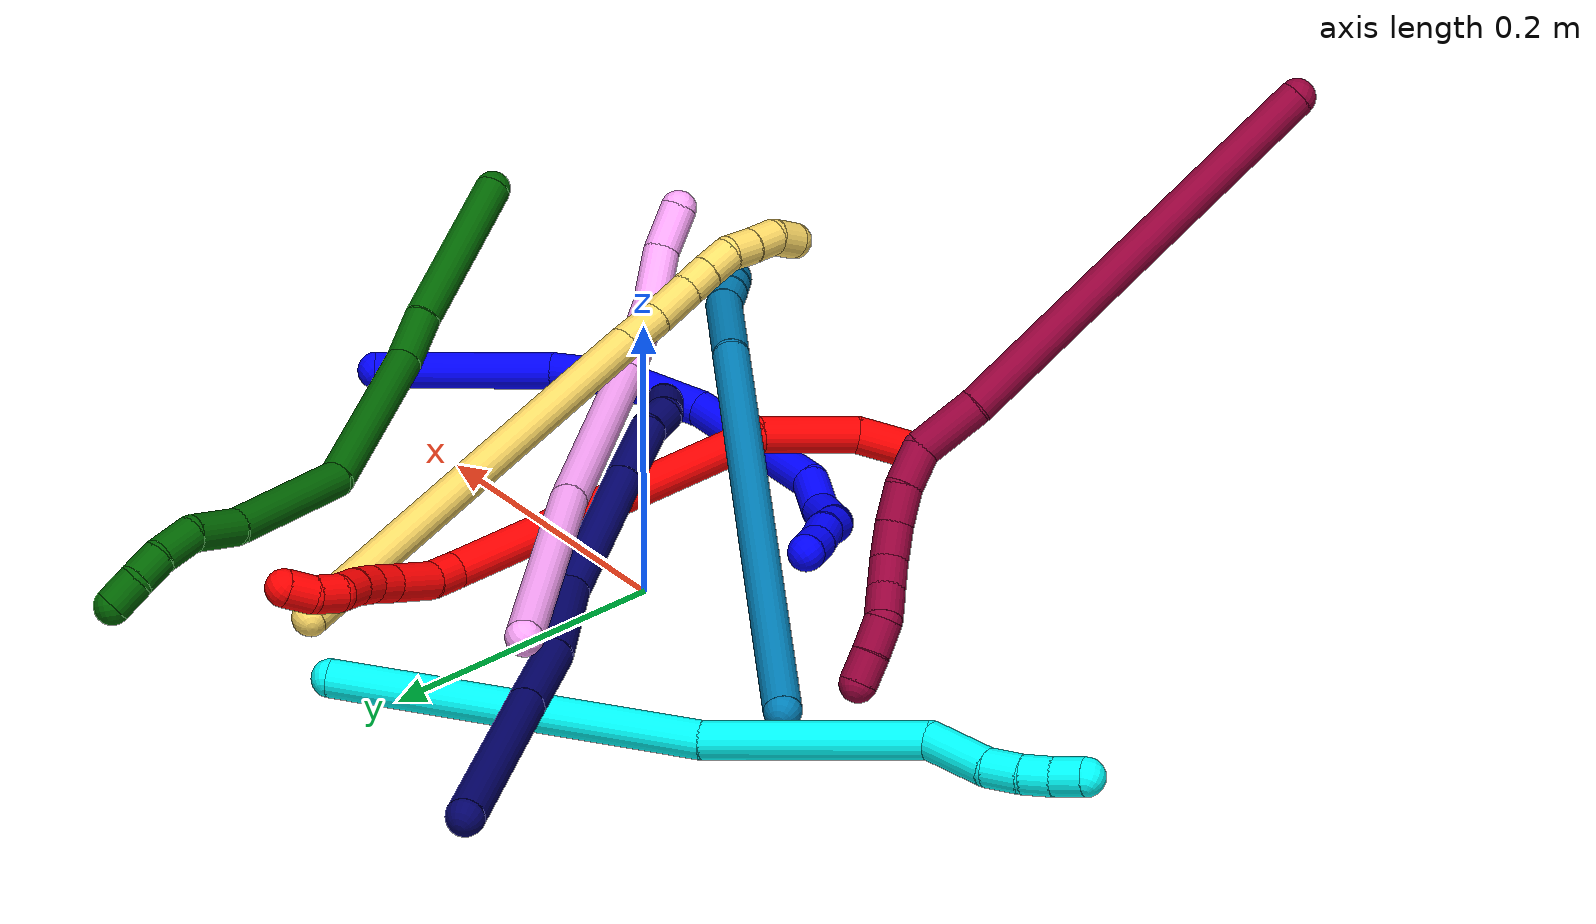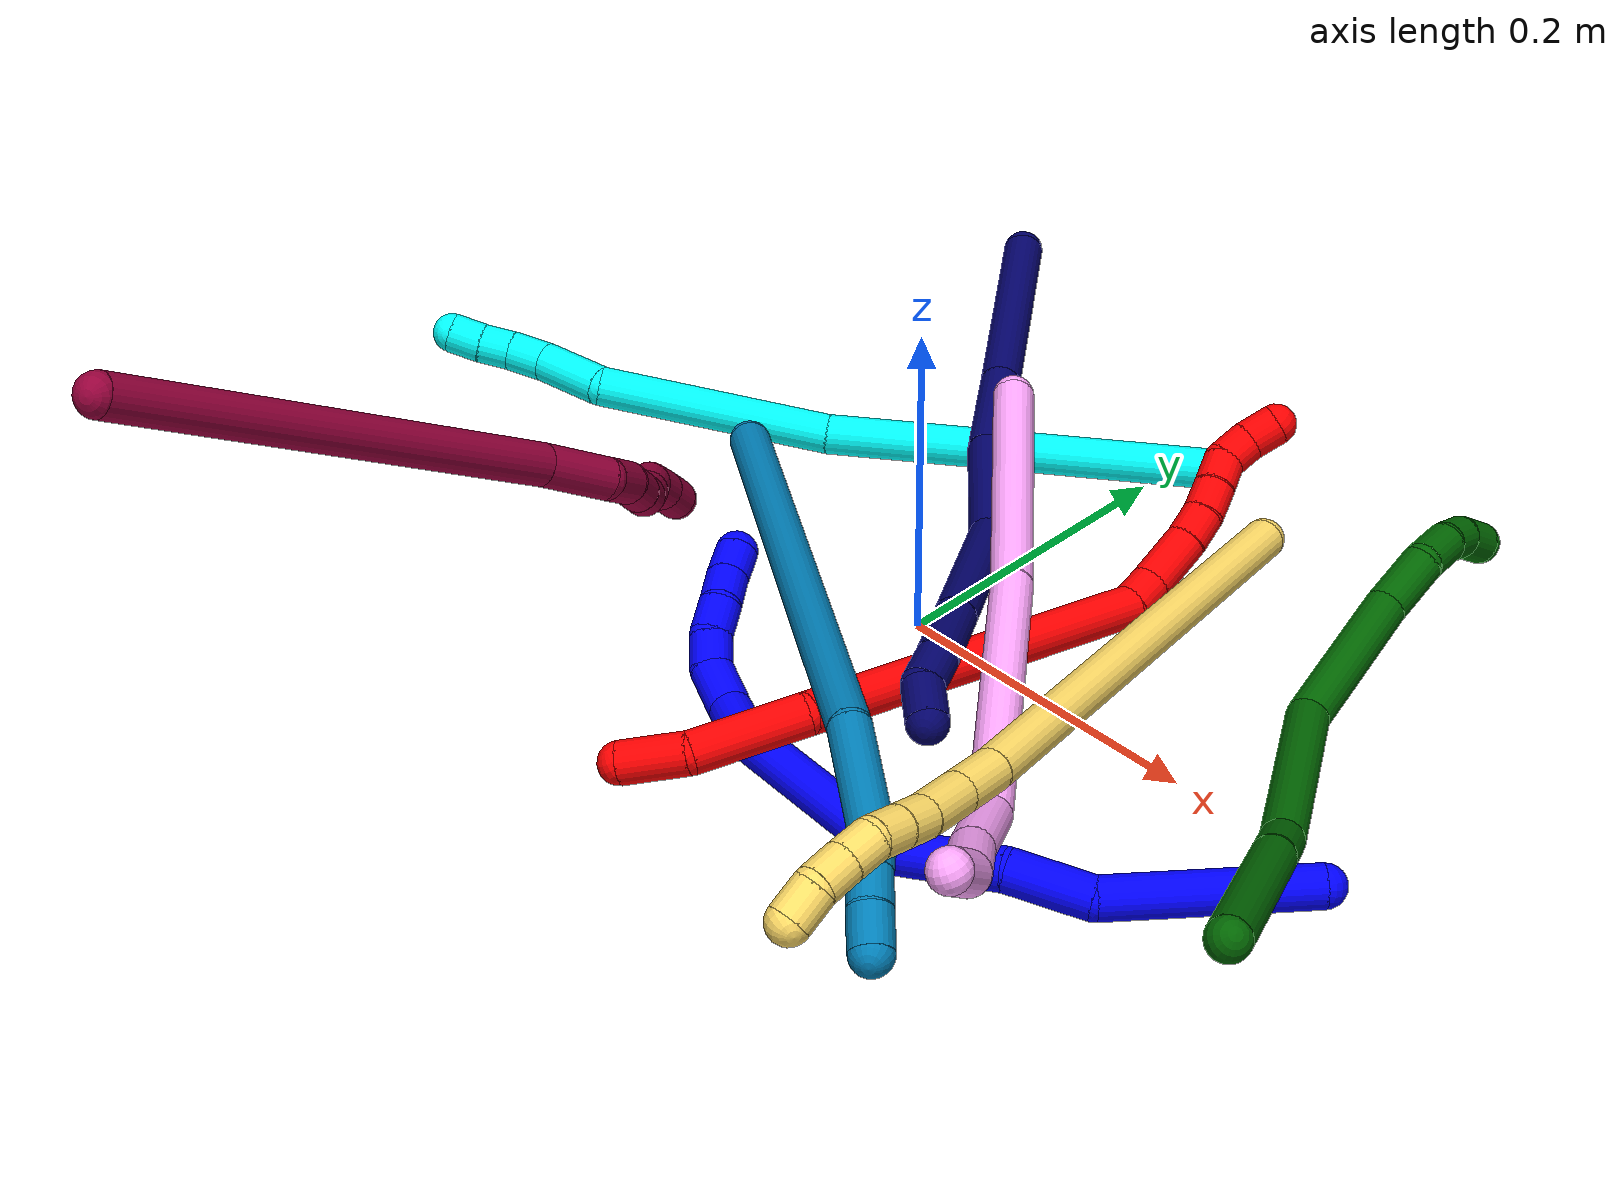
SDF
<sdf version="1.7">
 <world name="default">
  <plugin name="TubeGeneratorPlugin" filename="libtube_generator_plugin.so"/>
  <model name="photoneo_s_sensor">
   <static>1</static>
   <pose>0 0 2 1.57079 1.57079 3.14159</pose>
   <link name="link">
    <inertial><mass>0.1</mass></inertial>
    <sensor name="sensor" type="depth">
     <update_rate>30</update_rate>
     <camera>
      <horizontal_fov>1.22</horizontal_fov>
      <image><width>1920</width><height>1200</height><format>B8G8R8</format></image>
      <clip><near>0.1</near><far>4</far></clip>
      <depth_camera><output>points</output></depth_camera>
     </camera>
     <plugin name="camera_plugin" filename="libgazebo_ros_depth_camera.so">
      <baseline>0.2</baseline>
      <alwaysOn>1</alwaysOn>
      <updateRate>0.0</updateRate>
      <cameraName>camera_ir</cameraName>
      <imageTopicName>/camera/color/image_raw</imageTopicName>
      <cameraInfoTopicName>/camera/color/camera_info</cameraInfoTopicName>
      <depthImageTopicName>/camera/depth/image_raw</depthImageTopicName>
      <depthImageCameraInfoTopicName>/camera/depth/camera_info</depthImageCameraInfoTopicName>
      <pointCloudTopicName>/camera/depth/points</pointCloudTopicName>
      <frameName>fr_optical</frameName>
      <pointCloudCutoff>0.1</pointCloudCutoff>
      <pointCloudCutoffMax>2.0</pointCloudCutoffMax>
      <distortionK1>0</distortionK1>
      <distortionK2>0</distortionK2>
      <distortionK3>0</distortionK3>
      <distortionT1>0</distortionT1>
      <distortionT2>0</distortionT2>
      <CxPrime>0</CxPrime>
      <Cx>0</Cx>
      <Cy>0</Cy>
      <focalLength>0</focalLength>
      <hackBaseline>0</hackBaseline>
     </plugin>
    </sensor>
   </link>
  </model>
  <gravity>0 0 -9.8</gravity>
  <magnetic_field>6e-06 2.3e-05 -4.2e-05</magnetic_field>
  <atmosphere type="adiabatic"/>
  <physics name="default_physics" default="0" type="ode">
   <max_step_size>0.003</max_step_size>
   <real_time_factor>1</real_time_factor>
   <real_time_update_rate>1000</real_time_update_rate>
   <max_contacts>10000</max_contacts>
   <ode>
    <solver>
     <type>quick</type>
     <iters>100</iters>
     <sor>1.3</sor>
     <use_dynamic_moi_rescaling>0</use_dynamic_moi_rescaling>
    </solver>
    <constraints>
     <contact_max_correcting_vel>0</contact_max_correcting_vel>
     <contact_surface_layer>0.001</contact_surface_layer>
     <cfm>0</cfm>
     <erp>0.2</erp>
    </constraints>
   </ode>
  </physics>
  <scene><ambient>0.4 0.4 0.4 1</ambient><background>0.7 0.7 0.7 1</background><shadows>0</shadows></scene>
  <audio><device>default</device></audio>
  <spherical_coordinates>
   <surface_model>EARTH_WGS84</surface_model>
   <latitude_deg>0</latitude_deg>
   <longitude_deg>0</longitude_deg>
   <elevation>0</elevation>
   <heading_deg>0</heading_deg>
  </spherical_coordinates>
  <model name="bin">
   <static>1</static>
   <link name="bottom">
    <collision name="collision-bottom">
     <pose>0 0 -0.01 0 -0 0</pose>
     <geometry><box><size>0.8 0.6 0.02</size></box></geometry>
     <surface>
      <friction><ode><mu>100</mu><mu2>100</mu2></ode></friction>
      <contact><collide_bitmask>65535</collide_bitmask></contact>
     </surface>
    </collision>
   </link>
   <link name="west_wall">
    <collision name="collision-west_wall">
     <pose>-0.41 0 0.1 0 -0 0</pose>
     <geometry><box><size>0.02 0.6 0.2</size></box></geometry>
     <surface>
      <friction><ode><mu>100</mu><mu2>100</mu2></ode></friction>
      <contact><collide_bitmask>65535</collide_bitmask></contact>
     </surface>
    </collision>
   </link>
   <link name="east_wall">
    <collision name="collision-east_wall">
     <pose>0.41 0 0.1 0 -0 0</pose>
     <geometry><box><size>0.02 0.6 0.2</size></box></geometry>
     <surface>
      <friction><ode><mu>100</mu><mu2>100</mu2></ode></friction>
      <contact><collide_bitmask>65535</collide_bitmask></contact>
     </surface>
    </collision>
   </link>
   <link name="south_wall">
    <collision name="collision-south_wall">
     <pose>0 -0.31 0.1 0 -0 0</pose>
     <geometry><box><size>0.8 0.02 0.2</size></box></geometry>
     <surface>
      <friction><ode><mu>100</mu><mu2>100</mu2></ode></friction>
      <contact><collide_bitmask>65535</collide_bitmask></contact>
     </surface>
    </collision>
   </link>
   <link name="north_wall">
    <collision name="collision-north_wall">
     <pose>0 0.31 0.1 0 -0 0</pose>
     <geometry><box><size>0.8 0.02 0.2</size></box></geometry>
     <surface>
      <friction><ode><mu>100</mu><mu2>100</mu2></ode></friction>
      <contact><collide_bitmask>65535</collide_bitmask></contact>
     </surface>
    </collision>
   </link>
  </model>
  <model name="1">
   <static>0</static>
   <link name="1">
    <collision name="collision-cylinder-e_1_1_4">
     <pose>-0.02764 -0.025324 0.04775 0.487623 -0.472709 -0.119688</pose>
     <geometry><cylinder><radius>0.0125</radius><length>0.121413</length></cylinder></geometry>
     <surface>
      <friction><ode><mu>1.16</mu><mu2>1.16</mu2><slip1>0</slip1><slip2>0</slip2></ode></friction>
      <contact><ode><kp>1e+06</kp><kd>1</kd><max_vel>0</max_vel><min_depth>0.001</min_depth></ode></contact>
     </surface>
    </collision>
    <visual name="visual-cylinder-e_1_1_4">
     <pose>-0.02764 -0.025324 0.04775 0.487623 -0.472709 -0.119688</pose>
     <geometry><cylinder><radius>0.0125</radius><length>0.121413</length></cylinder></geometry>
     <material><ambient>0 0 1 1</ambient></material>
    </visual>
    <collision name="collision-cylinder-e_2_4_5">
     <pose>-0.074391 -0.05725 0.109239 0.448012 -0.897511 -0.218536</pose>
     <geometry><cylinder><radius>0.0125</radius><length>0.048894</length></cylinder></geometry>
     <surface>
      <friction><ode><mu>1.16</mu><mu2>1.16</mu2><slip1>0</slip1><slip2>0</slip2></ode></friction>
      <contact><ode><kp>1e+06</kp><kd>1</kd><max_vel>0</max_vel><min_depth>0.001</min_depth></ode></contact>
     </surface>
    </collision>
    <visual name="visual-cylinder-e_2_4_5">
     <pose>-0.074391 -0.05725 0.109239 0.448012 -0.897511 -0.218536</pose>
     <geometry><cylinder><radius>0.0125</radius><length>0.048894</length></cylinder></geometry>
     <material><ambient>0 0 1 1</ambient></material>
    </visual>
    <collision name="collision-cylinder-e_3_5_6">
     <pose>-0.117673 -0.07959 0.137143 0.837914 -0.851427 -0.398498</pose>
     <geometry><cylinder><radius>0.0125</radius><length>0.064264</length></cylinder></geometry>
     <surface>
      <friction><ode><mu>1.16</mu><mu2>1.16</mu2><slip1>0</slip1><slip2>0</slip2></ode></friction>
      <contact><ode><kp>1e+06</kp><kd>1</kd><max_vel>0</max_vel><min_depth>0.001</min_depth></ode></contact>
     </surface>
    </collision>
    <visual name="visual-cylinder-e_3_5_6">
     <pose>-0.117673 -0.07959 0.137143 0.837914 -0.851427 -0.398498</pose>
     <geometry><cylinder><radius>0.0125</radius><length>0.064264</length></cylinder></geometry>
     <material><ambient>0 0 1 1</ambient></material>
    </visual>
    <collision name="collision-cylinder-e_4_6_7">
     <pose>-0.200979 -0.109463 0.156108 1.24344 -1.32348 -1.01806</pose>
     <geometry><cylinder><radius>0.0125</radius><length>0.121982</length></cylinder></geometry>
     <surface>
      <friction><ode><mu>1.16</mu><mu2>1.16</mu2><slip1>0</slip1><slip2>0</slip2></ode></friction>
      <contact><ode><kp>1e+06</kp><kd>1</kd><max_vel>0</max_vel><min_depth>0.001</min_depth></ode></contact>
     </surface>
    </collision>
    <visual name="visual-cylinder-e_4_6_7">
     <pose>-0.200979 -0.109463 0.156108 1.24344 -1.32348 -1.01806</pose>
     <geometry><cylinder><radius>0.0125</radius><length>0.121982</length></cylinder></geometry>
     <material><ambient>0 0 1 1</ambient></material>
    </visual>
    <collision name="collision-cylinder-e_5_7_8">
     <pose>-0.273729 -0.127041 0.155318 2.59 -1.12153 -2.29481</pose>
     <geometry><cylinder><radius>0.0125</radius><length>0.030231</length></cylinder></geometry>
     <surface>
      <friction><ode><mu>1.16</mu><mu2>1.16</mu2><slip1>0</slip1><slip2>0</slip2></ode></friction>
      <contact><ode><kp>1e+06</kp><kd>1</kd><max_vel>0</max_vel><min_depth>0.001</min_depth></ode></contact>
     </surface>
    </collision>
    <visual name="visual-cylinder-e_5_7_8">
     <pose>-0.273729 -0.127041 0.155318 2.59 -1.12153 -2.29481</pose>
     <geometry><cylinder><radius>0.0125</radius><length>0.030231</length></cylinder></geometry>
     <material><ambient>0 0 1 1</ambient></material>
    </visual>
    <collision name="collision-cylinder-e_6_8_9">
     <pose>-0.302064 -0.129254 0.147658 -2.60607 -1.40878 2.51705</pose>
     <geometry><cylinder><radius>0.0125</radius><length>0.029828</length></cylinder></geometry>
     <surface>
      <friction><ode><mu>1.16</mu><mu2>1.16</mu2><slip1>0</slip1><slip2>0</slip2></ode></friction>
      <contact><ode><kp>1e+06</kp><kd>1</kd><max_vel>0</max_vel><min_depth>0.001</min_depth></ode></contact>
     </surface>
    </collision>
    <visual name="visual-cylinder-e_6_8_9">
     <pose>-0.302064 -0.129254 0.147658 -2.60607 -1.40878 2.51705</pose>
     <geometry><cylinder><radius>0.0125</radius><length>0.029828</length></cylinder></geometry>
     <material><ambient>0 0 1 1</ambient></material>
    </visual>
    <collision name="collision-cylinder-e_7_9_10">
     <pose>-0.325315 -0.123306 0.142708 -2.11872 -0.995814 1.53884</pose>
     <geometry><cylinder><radius>0.0125</radius><length>0.020336</length></cylinder></geometry>
     <surface>
      <friction><ode><mu>1.16</mu><mu2>1.16</mu2><slip1>0</slip1><slip2>0</slip2></ode></friction>
      <contact><ode><kp>1e+06</kp><kd>1</kd><max_vel>0</max_vel><min_depth>0.001</min_depth></ode></contact>
     </surface>
    </collision>
    <visual name="visual-cylinder-e_7_9_10">
     <pose>-0.325315 -0.123306 0.142708 -2.11872 -0.995814 1.53884</pose>
     <geometry><cylinder><radius>0.0125</radius><length>0.020336</length></cylinder></geometry>
     <material><ambient>0 0 1 1</ambient></material>
    </visual>
    <collision name="collision-cylinder-e_8_10_11">
     <pose>-0.341383 -0.113893 0.133859 -2.47527 -0.78151 1.74418</pose>
     <geometry><cylinder><radius>0.0125</radius><length>0.021394</length></cylinder></geometry>
     <surface>
      <friction><ode><mu>1.16</mu><mu2>1.16</mu2><slip1>0</slip1><slip2>0</slip2></ode></friction>
      <contact><ode><kp>1e+06</kp><kd>1</kd><max_vel>0</max_vel><min_depth>0.001</min_depth></ode></contact>
     </surface>
    </collision>
    <visual name="visual-cylinder-e_8_10_11">
     <pose>-0.341383 -0.113893 0.133859 -2.47527 -0.78151 1.74418</pose>
     <geometry><cylinder><radius>0.0125</radius><length>0.021394</length></cylinder></geometry>
     <material><ambient>0 0 1 1</ambient></material>
    </visual>
    <collision name="collision-cylinder-e_9_11_12">
     <pose>-0.357005 -0.106862 0.121235 -2.80374 -0.853615 2.42399</pose>
     <geometry><cylinder><radius>0.0125</radius><length>0.021463</length></cylinder></geometry>
     <surface>
      <friction><ode><mu>1.16</mu><mu2>1.16</mu2><slip1>0</slip1><slip2>0</slip2></ode></friction>
      <contact><ode><kp>1e+06</kp><kd>1</kd><max_vel>0</max_vel><min_depth>0.001</min_depth></ode></contact>
     </surface>
    </collision>
    <visual name="visual-cylinder-e_9_11_12">
     <pose>-0.357005 -0.106862 0.121235 -2.80374 -0.853615 2.42399</pose>
     <geometry><cylinder><radius>0.0125</radius><length>0.021463</length></cylinder></geometry>
     <material><ambient>0 0 1 1</ambient></material>
    </visual>
    <collision name="collision-cylinder-e_10_12_2">
     <pose>-0.372104 -0.101134 0.108152 -2.65631 -0.767498 2.04172</pose>
     <geometry><cylinder><radius>0.0125</radius><length>0.020197</length></cylinder></geometry>
     <surface>
      <friction><ode><mu>1.16</mu><mu2>1.16</mu2><slip1>0</slip1><slip2>0</slip2></ode></friction>
      <contact><ode><kp>1e+06</kp><kd>1</kd><max_vel>0</max_vel><min_depth>0.001</min_depth></ode></contact>
     </surface>
    </collision>
    <visual name="visual-cylinder-e_10_12_2">
     <pose>-0.372104 -0.101134 0.108152 -2.65631 -0.767498 2.04172</pose>
     <geometry><cylinder><radius>0.0125</radius><length>0.020197</length></cylinder></geometry>
     <material><ambient>0 0 1 1</ambient></material>
    </visual>
    <collision name="collision-sphere-2">
     <pose>-0.379116 -0.097744 0.101724 0 -0 0</pose>
     <geometry><sphere><radius>0.0125</radius></sphere></geometry>
     <surface>
      <friction><ode><mu>1.16</mu><mu2>1.16</mu2><slip1>0</slip1><slip2>0</slip2></ode></friction>
      <contact><ode><kp>1e+06</kp><kd>1</kd><max_vel>0</max_vel><min_depth>0.001</min_depth></ode></contact>
     </surface>
    </collision>
    <visual name="visual-sphere-2">
     <pose>-0.379116 -0.097744 0.101724 0 -0 0</pose>
     <geometry><sphere><radius>0.0125</radius></sphere></geometry>
     <material><ambient>0 0 1 1</ambient></material>
    </visual>
    <collision name="collision-sphere-12">
     <pose>-0.365093 -0.104524 0.114581 0 -0 0</pose>
     <geometry><sphere><radius>0.0125</radius></sphere></geometry>
     <surface>
      <friction><ode><mu>1.16</mu><mu2>1.16</mu2><slip1>0</slip1><slip2>0</slip2></ode></friction>
      <contact><ode><kp>1e+06</kp><kd>1</kd><max_vel>0</max_vel><min_depth>0.001</min_depth></ode></contact>
     </surface>
    </collision>
    <visual name="visual-sphere-12">
     <pose>-0.365093 -0.104524 0.114581 0 -0 0</pose>
     <geometry><sphere><radius>0.0125</radius></sphere></geometry>
     <material><ambient>0 0 1 1</ambient></material>
    </visual>
    <collision name="collision-sphere-11">
     <pose>-0.348917 -0.109199 0.12789 0 -0 0</pose>
     <geometry><sphere><radius>0.0125</radius></sphere></geometry>
     <surface>
      <friction><ode><mu>1.16</mu><mu2>1.16</mu2><slip1>0</slip1><slip2>0</slip2></ode></friction>
      <contact><ode><kp>1e+06</kp><kd>1</kd><max_vel>0</max_vel><min_depth>0.001</min_depth></ode></contact>
     </surface>
    </collision>
    <visual name="visual-sphere-11">
     <pose>-0.348917 -0.109199 0.12789 0 -0 0</pose>
     <geometry><sphere><radius>0.0125</radius></sphere></geometry>
     <material><ambient>0 0 1 1</ambient></material>
    </visual>
    <collision name="collision-sphere-10">
     <pose>-0.333848 -0.118586 0.139828 0 -0 0</pose>
     <geometry><sphere><radius>0.0125</radius></sphere></geometry>
     <surface>
      <friction><ode><mu>1.16</mu><mu2>1.16</mu2><slip1>0</slip1><slip2>0</slip2></ode></friction>
      <contact><ode><kp>1e+06</kp><kd>1</kd><max_vel>0</max_vel><min_depth>0.001</min_depth></ode></contact>
     </surface>
    </collision>
    <visual name="visual-sphere-10">
     <pose>-0.333848 -0.118586 0.139828 0 -0 0</pose>
     <geometry><sphere><radius>0.0125</radius></sphere></geometry>
     <material><ambient>0 0 1 1</ambient></material>
    </visual>
    <collision name="collision-sphere-9">
     <pose>-0.316782 -0.128026 0.145589 0 -0 0</pose>
     <geometry><sphere><radius>0.0125</radius></sphere></geometry>
     <surface>
      <friction><ode><mu>1.16</mu><mu2>1.16</mu2><slip1>0</slip1><slip2>0</slip2></ode></friction>
      <contact><ode><kp>1e+06</kp><kd>1</kd><max_vel>0</max_vel><min_depth>0.001</min_depth></ode></contact>
     </surface>
    </collision>
    <visual name="visual-sphere-9">
     <pose>-0.316782 -0.128026 0.145589 0 -0 0</pose>
     <geometry><sphere><radius>0.0125</radius></sphere></geometry>
     <material><ambient>0 0 1 1</ambient></material>
    </visual>
    <collision name="collision-sphere-4">
     <pose>-0.055279 -0.050647 0.095499 0 -0 0</pose>
     <geometry><sphere><radius>0.0125</radius></sphere></geometry>
     <surface>
      <friction><ode><mu>1.16</mu><mu2>1.16</mu2><slip1>0</slip1><slip2>0</slip2></ode></friction>
      <contact><ode><kp>1e+06</kp><kd>1</kd><max_vel>0</max_vel><min_depth>0.001</min_depth></ode></contact>
     </surface>
    </collision>
    <visual name="visual-sphere-4">
     <pose>-0.055279 -0.050647 0.095499 0 -0 0</pose>
     <geometry><sphere><radius>0.0125</radius></sphere></geometry>
     <material><ambient>0 0 1 1</ambient></material>
    </visual>
    <collision name="collision-sphere-1">
     <geometry><sphere><radius>0.0125</radius></sphere></geometry>
     <surface>
      <friction><ode><mu>1.16</mu><mu2>1.16</mu2><slip1>0</slip1><slip2>0</slip2></ode></friction>
      <contact><ode><kp>1e+06</kp><kd>1</kd><max_vel>0</max_vel><min_depth>0.001</min_depth></ode></contact>
     </surface>
    </collision>
    <visual name="visual-sphere-1">
     <geometry><sphere><radius>0.0125</radius></sphere></geometry>
     <material><ambient>0 0 1 1</ambient></material>
    </visual>
    <collision name="collision-sphere-8">
     <pose>-0.287345 -0.130481 0.149727 0 -0 0</pose>
     <geometry><sphere><radius>0.0125</radius></sphere></geometry>
     <surface>
      <friction><ode><mu>1.16</mu><mu2>1.16</mu2><slip1>0</slip1><slip2>0</slip2></ode></friction>
      <contact><ode><kp>1e+06</kp><kd>1</kd><max_vel>0</max_vel><min_depth>0.001</min_depth></ode></contact>
     </surface>
    </collision>
    <visual name="visual-sphere-8">
     <pose>-0.287345 -0.130481 0.149727 0 -0 0</pose>
     <geometry><sphere><radius>0.0125</radius></sphere></geometry>
     <material><ambient>0 0 1 1</ambient></material>
    </visual>
    <collision name="collision-sphere-5">
     <pose>-0.093503 -0.063854 0.122979 0 -0 0</pose>
     <geometry><sphere><radius>0.0125</radius></sphere></geometry>
     <surface>
      <friction><ode><mu>1.16</mu><mu2>1.16</mu2><slip1>0</slip1><slip2>0</slip2></ode></friction>
      <contact><ode><kp>1e+06</kp><kd>1</kd><max_vel>0</max_vel><min_depth>0.001</min_depth></ode></contact>
     </surface>
    </collision>
    <visual name="visual-sphere-5">
     <pose>-0.093503 -0.063854 0.122979 0 -0 0</pose>
     <geometry><sphere><radius>0.0125</radius></sphere></geometry>
     <material><ambient>0 0 1 1</ambient></material>
    </visual>
    <collision name="collision-sphere-6">
     <pose>-0.141844 -0.095326 0.151307 0 -0 0</pose>
     <geometry><sphere><radius>0.0125</radius></sphere></geometry>
     <surface>
      <friction><ode><mu>1.16</mu><mu2>1.16</mu2><slip1>0</slip1><slip2>0</slip2></ode></friction>
      <contact><ode><kp>1e+06</kp><kd>1</kd><max_vel>0</max_vel><min_depth>0.001</min_depth></ode></contact>
     </surface>
    </collision>
    <visual name="visual-sphere-6">
     <pose>-0.141844 -0.095326 0.151307 0 -0 0</pose>
     <geometry><sphere><radius>0.0125</radius></sphere></geometry>
     <material><ambient>0 0 1 1</ambient></material>
    </visual>
    <collision name="collision-sphere-7">
     <pose>-0.260114 -0.123601 0.160909 0 -0 0</pose>
     <geometry><sphere><radius>0.0125</radius></sphere></geometry>
     <surface>
      <friction><ode><mu>1.16</mu><mu2>1.16</mu2><slip1>0</slip1><slip2>0</slip2></ode></friction>
      <contact><ode><kp>1e+06</kp><kd>1</kd><max_vel>0</max_vel><min_depth>0.001</min_depth></ode></contact>
     </surface>
    </collision>
    <visual name="visual-sphere-7">
     <pose>-0.260114 -0.123601 0.160909 0 -0 0</pose>
     <geometry><sphere><radius>0.0125</radius></sphere></geometry>
     <material><ambient>0 0 1 1</ambient></material>
    </visual>
    <inertial>
     <pose>-0.170905 -0.082635 0.117292 0 -0 0</pose>
     <mass>0.5</mass>
     <inertia>
      <ixx>9.2e-05</ixx>
      <ixy>0</ixy>
      <ixz>0</ixz>
      <iyy>0.000268</iyy>
      <iyz>0</iyz>
      <izz>0.000382</izz>
     </inertia>
    </inertial>
   </link>
   <pose>0.317458 -0.019085 0.012481 1.1968 0.224847 -0.210768</pose>
  </model>
  <model name="2">
   <static>0</static>
   <link name="2">
    <collision name="collision-cylinder-e_1_1_4">
     <pose>-0.013801 0.012202 0.007673 -1.00943 -0.763689 0.4366</pose>
     <geometry><cylinder><radius>0.0125</radius><length>0.039911</length></cylinder></geometry>
     <surface>
      <friction><ode><mu>1.16</mu><mu2>1.16</mu2><slip1>0</slip1><slip2>0</slip2></ode></friction>
      <contact><ode><kp>1e+06</kp><kd>1</kd><max_vel>0</max_vel><min_depth>0.001</min_depth></ode></contact>
     </surface>
    </collision>
    <visual name="visual-cylinder-e_1_1_4">
     <pose>-0.013801 0.012202 0.007673 -1.00943 -0.763689 0.4366</pose>
     <geometry><cylinder><radius>0.0125</radius><length>0.039911</length></cylinder></geometry>
     <material><ambient>1 0 0 1</ambient></material>
    </visual>
    <collision name="collision-cylinder-e_2_4_5">
     <pose>-0.04018 0.052833 0.028606 -1.13438 -0.381315 0.24466</pose>
     <geometry><cylinder><radius>0.0125</radius><length>0.067595</length></cylinder></geometry>
     <surface>
      <friction><ode><mu>1.16</mu><mu2>1.16</mu2><slip1>0</slip1><slip2>0</slip2></ode></friction>
      <contact><ode><kp>1e+06</kp><kd>1</kd><max_vel>0</max_vel><min_depth>0.001</min_depth></ode></contact>
     </surface>
    </collision>
    <visual name="visual-cylinder-e_2_4_5">
     <pose>-0.04018 0.052833 0.028606 -1.13438 -0.381315 0.24466</pose>
     <geometry><cylinder><radius>0.0125</radius><length>0.067595</length></cylinder></geometry>
     <material><ambient>1 0 0 1</ambient></material>
    </visual>
    <collision name="collision-cylinder-e_3_5_6">
     <pose>-0.051136 0.181959 0.100742 -1.04171 0.0139 -0.007975</pose>
     <geometry><cylinder><radius>0.0125</radius><length>0.233314</length></cylinder></geometry>
     <surface>
      <friction><ode><mu>1.16</mu><mu2>1.16</mu2><slip1>0</slip1><slip2>0</slip2></ode></friction>
      <contact><ode><kp>1e+06</kp><kd>1</kd><max_vel>0</max_vel><min_depth>0.001</min_depth></ode></contact>
     </surface>
    </collision>
    <visual name="visual-cylinder-e_3_5_6">
     <pose>-0.051136 0.181959 0.100742 -1.04171 0.0139 -0.007975</pose>
     <geometry><cylinder><radius>0.0125</radius><length>0.233314</length></cylinder></geometry>
     <material><ambient>1 0 0 1</ambient></material>
    </visual>
    <collision name="collision-cylinder-e_4_6_7">
     <pose>-0.047863 0.293553 0.161265 -1.42082 0.148724 -0.128</pose>
     <geometry><cylinder><radius>0.0125</radius><length>0.022288</length></cylinder></geometry>
     <surface>
      <friction><ode><mu>1.16</mu><mu2>1.16</mu2><slip1>0</slip1><slip2>0</slip2></ode></friction>
      <contact><ode><kp>1e+06</kp><kd>1</kd><max_vel>0</max_vel><min_depth>0.001</min_depth></ode></contact>
     </surface>
    </collision>
    <visual name="visual-cylinder-e_4_6_7">
     <pose>-0.047863 0.293553 0.161265 -1.42082 0.148724 -0.128</pose>
     <geometry><cylinder><radius>0.0125</radius><length>0.022288</length></cylinder></geometry>
     <material><ambient>1 0 0 1</ambient></material>
    </visual>
    <collision name="collision-cylinder-e_5_7_8">
     <pose>-0.047019 0.322382 0.162849 -1.57427 -0.04498 0.045136</pose>
     <geometry><cylinder><radius>0.0125</radius><length>0.035899</length></cylinder></geometry>
     <surface>
      <friction><ode><mu>1.16</mu><mu2>1.16</mu2><slip1>0</slip1><slip2>0</slip2></ode></friction>
      <contact><ode><kp>1e+06</kp><kd>1</kd><max_vel>0</max_vel><min_depth>0.001</min_depth></ode></contact>
     </surface>
    </collision>
    <visual name="visual-cylinder-e_5_7_8">
     <pose>-0.047019 0.322382 0.162849 -1.57427 -0.04498 0.045136</pose>
     <geometry><cylinder><radius>0.0125</radius><length>0.035899</length></cylinder></geometry>
     <material><ambient>1 0 0 1</ambient></material>
    </visual>
    <collision name="collision-cylinder-e_6_8_9">
     <pose>-0.047787 0.350533 0.161699 -1.67684 0.003784 -0.004208</pose>
     <geometry><cylinder><radius>0.0125</radius><length>0.020555</length></cylinder></geometry>
     <surface>
      <friction><ode><mu>1.16</mu><mu2>1.16</mu2><slip1>0</slip1><slip2>0</slip2></ode></friction>
      <contact><ode><kp>1e+06</kp><kd>1</kd><max_vel>0</max_vel><min_depth>0.001</min_depth></ode></contact>
     </surface>
    </collision>
    <visual name="visual-cylinder-e_6_8_9">
     <pose>-0.047787 0.350533 0.161699 -1.67684 0.003784 -0.004208</pose>
     <geometry><cylinder><radius>0.0125</radius><length>0.020555</length></cylinder></geometry>
     <material><ambient>1 0 0 1</ambient></material>
    </visual>
    <collision name="collision-cylinder-e_7_9_10">
     <pose>-0.046275 0.370437 0.15859 -1.7766 0.147865 -0.181751</pose>
     <geometry><cylinder><radius>0.0125</radius><length>0.020004</length></cylinder></geometry>
     <surface>
      <friction><ode><mu>1.16</mu><mu2>1.16</mu2><slip1>0</slip1><slip2>0</slip2></ode></friction>
      <contact><ode><kp>1e+06</kp><kd>1</kd><max_vel>0</max_vel><min_depth>0.001</min_depth></ode></contact>
     </surface>
    </collision>
    <visual name="visual-cylinder-e_7_9_10">
     <pose>-0.046275 0.370437 0.15859 -1.7766 0.147865 -0.181751</pose>
     <geometry><cylinder><radius>0.0125</radius><length>0.020004</length></cylinder></geometry>
     <material><ambient>1 0 0 1</ambient></material>
    </visual>
    <collision name="collision-cylinder-e_8_10_11">
     <pose>-0.042381 0.389764 0.154961 -1.736 0.242659 -0.285915</pose>
     <geometry><cylinder><radius>0.0125</radius><length>0.020142</length></cylinder></geometry>
     <surface>
      <friction><ode><mu>1.16</mu><mu2>1.16</mu2><slip1>0</slip1><slip2>0</slip2></ode></friction>
      <contact><ode><kp>1e+06</kp><kd>1</kd><max_vel>0</max_vel><min_depth>0.001</min_depth></ode></contact>
     </surface>
    </collision>
    <visual name="visual-cylinder-e_8_10_11">
     <pose>-0.042381 0.389764 0.154961 -1.736 0.242659 -0.285915</pose>
     <geometry><cylinder><radius>0.0125</radius><length>0.020142</length></cylinder></geometry>
     <material><ambient>1 0 0 1</ambient></material>
    </visual>
    <collision name="collision-cylinder-e_9_11_12">
     <pose>-0.041295 0.409377 0.15461 -1.44535 -0.131998 0.116436</pose>
     <geometry><cylinder><radius>0.0125</radius><length>0.020275</length></cylinder></geometry>
     <surface>
      <friction><ode><mu>1.16</mu><mu2>1.16</mu2><slip1>0</slip1><slip2>0</slip2></ode></friction>
      <contact><ode><kp>1e+06</kp><kd>1</kd><max_vel>0</max_vel><min_depth>0.001</min_depth></ode></contact>
     </surface>
    </collision>
    <visual name="visual-cylinder-e_9_11_12">
     <pose>-0.041295 0.409377 0.15461 -1.44535 -0.131998 0.116436</pose>
     <geometry><cylinder><radius>0.0125</radius><length>0.020275</length></cylinder></geometry>
     <material><ambient>1 0 0 1</ambient></material>
    </visual>
    <collision name="collision-cylinder-e_10_12_2">
     <pose>-0.047313 0.428092 0.157198 -1.41983 -0.48697 0.42065</pose>
     <geometry><cylinder><radius>0.0125</radius><length>0.020017</length></cylinder></geometry>
     <surface>
      <friction><ode><mu>1.16</mu><mu2>1.16</mu2><slip1>0</slip1><slip2>0</slip2></ode></friction>
      <contact><ode><kp>1e+06</kp><kd>1</kd><max_vel>0</max_vel><min_depth>0.001</min_depth></ode></contact>
     </surface>
    </collision>
    <visual name="visual-cylinder-e_10_12_2">
     <pose>-0.047313 0.428092 0.157198 -1.41983 -0.48697 0.42065</pose>
     <geometry><cylinder><radius>0.0125</radius><length>0.020017</length></cylinder></geometry>
     <material><ambient>1 0 0 1</ambient></material>
    </visual>
    <collision name="collision-sphere-2">
     <pose>-0.051996 0.436836 0.158528 0 -0 0</pose>
     <geometry><sphere><radius>0.0125</radius></sphere></geometry>
     <surface>
      <friction><ode><mu>1.16</mu><mu2>1.16</mu2><slip1>0</slip1><slip2>0</slip2></ode></friction>
      <contact><ode><kp>1e+06</kp><kd>1</kd><max_vel>0</max_vel><min_depth>0.001</min_depth></ode></contact>
     </surface>
    </collision>
    <visual name="visual-sphere-2">
     <pose>-0.051996 0.436836 0.158528 0 -0 0</pose>
     <geometry><sphere><radius>0.0125</radius></sphere></geometry>
     <material><ambient>1 0 0 1</ambient></material>
    </visual>
    <collision name="collision-sphere-12">
     <pose>-0.04263 0.419347 0.155868 0 -0 0</pose>
     <geometry><sphere><radius>0.0125</radius></sphere></geometry>
     <surface>
      <friction><ode><mu>1.16</mu><mu2>1.16</mu2><slip1>0</slip1><slip2>0</slip2></ode></friction>
      <contact><ode><kp>1e+06</kp><kd>1</kd><max_vel>0</max_vel><min_depth>0.001</min_depth></ode></contact>
     </surface>
    </collision>
    <visual name="visual-sphere-12">
     <pose>-0.04263 0.419347 0.155868 0 -0 0</pose>
     <geometry><sphere><radius>0.0125</radius></sphere></geometry>
     <material><ambient>1 0 0 1</ambient></material>
    </visual>
    <collision name="collision-sphere-11">
     <pose>-0.039961 0.399406 0.153353 0 -0 0</pose>
     <geometry><sphere><radius>0.0125</radius></sphere></geometry>
     <surface>
      <friction><ode><mu>1.16</mu><mu2>1.16</mu2><slip1>0</slip1><slip2>0</slip2></ode></friction>
      <contact><ode><kp>1e+06</kp><kd>1</kd><max_vel>0</max_vel><min_depth>0.001</min_depth></ode></contact>
     </surface>
    </collision>
    <visual name="visual-sphere-11">
     <pose>-0.039961 0.399406 0.153353 0 -0 0</pose>
     <geometry><sphere><radius>0.0125</radius></sphere></geometry>
     <material><ambient>1 0 0 1</ambient></material>
    </visual>
    <collision name="collision-sphere-10">
     <pose>-0.044801 0.380121 0.156568 0 -0 0</pose>
     <geometry><sphere><radius>0.0125</radius></sphere></geometry>
     <surface>
      <friction><ode><mu>1.16</mu><mu2>1.16</mu2><slip1>0</slip1><slip2>0</slip2></ode></friction>
      <contact><ode><kp>1e+06</kp><kd>1</kd><max_vel>0</max_vel><min_depth>0.001</min_depth></ode></contact>
     </surface>
    </collision>
    <visual name="visual-sphere-10">
     <pose>-0.044801 0.380121 0.156568 0 -0 0</pose>
     <geometry><sphere><radius>0.0125</radius></sphere></geometry>
     <material><ambient>1 0 0 1</ambient></material>
    </visual>
    <collision name="collision-sphere-9">
     <pose>-0.047748 0.360753 0.160612 0 -0 0</pose>
     <geometry><sphere><radius>0.0125</radius></sphere></geometry>
     <surface>
      <friction><ode><mu>1.16</mu><mu2>1.16</mu2><slip1>0</slip1><slip2>0</slip2></ode></friction>
      <contact><ode><kp>1e+06</kp><kd>1</kd><max_vel>0</max_vel><min_depth>0.001</min_depth></ode></contact>
     </surface>
    </collision>
    <visual name="visual-sphere-9">
     <pose>-0.047748 0.360753 0.160612 0 -0 0</pose>
     <geometry><sphere><radius>0.0125</radius></sphere></geometry>
     <material><ambient>1 0 0 1</ambient></material>
    </visual>
    <collision name="collision-sphere-4">
     <pose>-0.027602 0.024403 0.015346 0 -0 0</pose>
     <geometry><sphere><radius>0.0125</radius></sphere></geometry>
     <surface>
      <friction><ode><mu>1.16</mu><mu2>1.16</mu2><slip1>0</slip1><slip2>0</slip2></ode></friction>
      <contact><ode><kp>1e+06</kp><kd>1</kd><max_vel>0</max_vel><min_depth>0.001</min_depth></ode></contact>
     </surface>
    </collision>
    <visual name="visual-sphere-4">
     <pose>-0.027602 0.024403 0.015346 0 -0 0</pose>
     <geometry><sphere><radius>0.0125</radius></sphere></geometry>
     <material><ambient>1 0 0 1</ambient></material>
    </visual>
    <collision name="collision-sphere-1">
     <geometry><sphere><radius>0.0125</radius></sphere></geometry>
     <surface>
      <friction><ode><mu>1.16</mu><mu2>1.16</mu2><slip1>0</slip1><slip2>0</slip2></ode></friction>
      <contact><ode><kp>1e+06</kp><kd>1</kd><max_vel>0</max_vel><min_depth>0.001</min_depth></ode></contact>
     </surface>
    </collision>
    <visual name="visual-sphere-1">
     <geometry><sphere><radius>0.0125</radius></sphere></geometry>
     <material><ambient>1 0 0 1</ambient></material>
    </visual>
    <collision name="collision-sphere-8">
     <pose>-0.047826 0.340313 0.162787 0 -0 0</pose>
     <geometry><sphere><radius>0.0125</radius></sphere></geometry>
     <surface>
      <friction><ode><mu>1.16</mu><mu2>1.16</mu2><slip1>0</slip1><slip2>0</slip2></ode></friction>
      <contact><ode><kp>1e+06</kp><kd>1</kd><max_vel>0</max_vel><min_depth>0.001</min_depth></ode></contact>
     </surface>
    </collision>
    <visual name="visual-sphere-8">
     <pose>-0.047826 0.340313 0.162787 0 -0 0</pose>
     <geometry><sphere><radius>0.0125</radius></sphere></geometry>
     <material><ambient>1 0 0 1</ambient></material>
    </visual>
    <collision name="collision-sphere-5">
     <pose>-0.052757 0.081263 0.041866 0 -0 0</pose>
     <geometry><sphere><radius>0.0125</radius></sphere></geometry>
     <surface>
      <friction><ode><mu>1.16</mu><mu2>1.16</mu2><slip1>0</slip1><slip2>0</slip2></ode></friction>
      <contact><ode><kp>1e+06</kp><kd>1</kd><max_vel>0</max_vel><min_depth>0.001</min_depth></ode></contact>
     </surface>
    </collision>
    <visual name="visual-sphere-5">
     <pose>-0.052757 0.081263 0.041866 0 -0 0</pose>
     <geometry><sphere><radius>0.0125</radius></sphere></geometry>
     <material><ambient>1 0 0 1</ambient></material>
    </visual>
    <collision name="collision-sphere-6">
     <pose>-0.049514 0.282656 0.159618 0 -0 0</pose>
     <geometry><sphere><radius>0.0125</radius></sphere></geometry>
     <surface>
      <friction><ode><mu>1.16</mu><mu2>1.16</mu2><slip1>0</slip1><slip2>0</slip2></ode></friction>
      <contact><ode><kp>1e+06</kp><kd>1</kd><max_vel>0</max_vel><min_depth>0.001</min_depth></ode></contact>
     </surface>
    </collision>
    <visual name="visual-sphere-6">
     <pose>-0.049514 0.282656 0.159618 0 -0 0</pose>
     <geometry><sphere><radius>0.0125</radius></sphere></geometry>
     <material><ambient>1 0 0 1</ambient></material>
    </visual>
    <collision name="collision-sphere-7">
     <pose>-0.046212 0.30445 0.162912 0 -0 0</pose>
     <geometry><sphere><radius>0.0125</radius></sphere></geometry>
     <surface>
      <friction><ode><mu>1.16</mu><mu2>1.16</mu2><slip1>0</slip1><slip2>0</slip2></ode></friction>
      <contact><ode><kp>1e+06</kp><kd>1</kd><max_vel>0</max_vel><min_depth>0.001</min_depth></ode></contact>
     </surface>
    </collision>
    <visual name="visual-sphere-7">
     <pose>-0.046212 0.30445 0.162912 0 -0 0</pose>
     <geometry><sphere><radius>0.0125</radius></sphere></geometry>
     <material><ambient>1 0 0 1</ambient></material>
    </visual>
    <inertial>
     <pose>-0.044996 0.207926 0.102167 0 -0 0</pose>
     <mass>0.5</mass>
     <inertia>
      <ixx>0.001107</ixx>
      <ixy>0</ixy>
      <ixz>0</ixz>
      <iyy>0.000592</iyy>
      <iyz>0</iyz>
      <izz>-0.00095</izz>
     </inertia>
    </inertial>
   </link>
   <pose>-0.007768 -0.224216 0.023149 2.75423 0.50948 3.05081</pose>
  </model>
  <model name="3">
   <static>0</static>
   <link name="3">
    <collision name="collision-cylinder-e_1_1_4">
     <pose>-0.081458 -0.090206 0.006492 1.49895 -0.733195 -0.686349</pose>
     <geometry><cylinder><radius>0.0125</radius><length>0.243431</length></cylinder></geometry>
     <surface>
      <friction><ode><mu>1.16</mu><mu2>1.16</mu2><slip1>0</slip1><slip2>0</slip2></ode></friction>
      <contact><ode><kp>1e+06</kp><kd>1</kd><max_vel>0</max_vel><min_depth>0.001</min_depth></ode></contact>
     </surface>
    </collision>
    <visual name="visual-cylinder-e_1_1_4">
     <pose>-0.081458 -0.090206 0.006492 1.49895 -0.733195 -0.686349</pose>
     <geometry><cylinder><radius>0.0125</radius><length>0.243431</length></cylinder></geometry>
     <material><ambient>0.003922 1 0.996078 1</ambient></material>
    </visual>
    <collision name="collision-cylinder-e_2_4_5">
     <pose>-0.203937 -0.240976 0.009463 1.62889 -0.594571 -0.627921</pose>
     <geometry><cylinder><radius>0.0125</radius><length>0.146467</length></cylinder></geometry>
     <surface>
      <friction><ode><mu>1.16</mu><mu2>1.16</mu2><slip1>0</slip1><slip2>0</slip2></ode></friction>
      <contact><ode><kp>1e+06</kp><kd>1</kd><max_vel>0</max_vel><min_depth>0.001</min_depth></ode></contact>
     </surface>
    </collision>
    <visual name="visual-cylinder-e_2_4_5">
     <pose>-0.203937 -0.240976 0.009463 1.62889 -0.594571 -0.627921</pose>
     <geometry><cylinder><radius>0.0125</radius><length>0.146467</length></cylinder></geometry>
     <material><ambient>0.003922 1 0.996078 1</ambient></material>
    </visual>
    <collision name="collision-cylinder-e_3_5_6">
     <pose>-0.254932 -0.319275 0.015962 1.05647 -0.455235 -0.268707</pose>
     <geometry><cylinder><radius>0.0125</radius><length>0.045362</length></cylinder></geometry>
     <surface>
      <friction><ode><mu>1.16</mu><mu2>1.16</mu2><slip1>0</slip1><slip2>0</slip2></ode></friction>
      <contact><ode><kp>1e+06</kp><kd>1</kd><max_vel>0</max_vel><min_depth>0.001</min_depth></ode></contact>
     </surface>
    </collision>
    <visual name="visual-cylinder-e_3_5_6">
     <pose>-0.254932 -0.319275 0.015962 1.05647 -0.455235 -0.268707</pose>
     <geometry><cylinder><radius>0.0125</radius><length>0.045362</length></cylinder></geometry>
     <material><ambient>0.003922 1 0.996078 1</ambient></material>
    </visual>
    <collision name="collision-cylinder-e_4_6_7">
     <pose>-0.270852 -0.34707 0.028367 1.33815 -0.52212 -0.416388</pose>
     <geometry><cylinder><radius>0.0125</radius><length>0.023853</length></cylinder></geometry>
     <surface>
      <friction><ode><mu>1.16</mu><mu2>1.16</mu2><slip1>0</slip1><slip2>0</slip2></ode></friction>
      <contact><ode><kp>1e+06</kp><kd>1</kd><max_vel>0</max_vel><min_depth>0.001</min_depth></ode></contact>
     </surface>
    </collision>
    <visual name="visual-cylinder-e_4_6_7">
     <pose>-0.270852 -0.34707 0.028367 1.33815 -0.52212 -0.416388</pose>
     <geometry><cylinder><radius>0.0125</radius><length>0.023853</length></cylinder></geometry>
     <material><ambient>0.003922 1 0.996078 1</ambient></material>
    </visual>
    <collision name="collision-cylinder-e_5_7_8">
     <pose>-0.282281 -0.365526 0.031205 1.51666 -0.577597 -0.54869</pose>
     <geometry><cylinder><radius>0.0125</radius><length>0.020077</length></cylinder></geometry>
     <surface>
      <friction><ode><mu>1.16</mu><mu2>1.16</mu2><slip1>0</slip1><slip2>0</slip2></ode></friction>
      <contact><ode><kp>1e+06</kp><kd>1</kd><max_vel>0</max_vel><min_depth>0.001</min_depth></ode></contact>
     </surface>
    </collision>
    <visual name="visual-cylinder-e_5_7_8">
     <pose>-0.282281 -0.365526 0.031205 1.51666 -0.577597 -0.54869</pose>
     <geometry><cylinder><radius>0.0125</radius><length>0.020077</length></cylinder></geometry>
     <material><ambient>0.003922 1 0.996078 1</ambient></material>
    </visual>
    <collision name="collision-cylinder-e_6_8_2">
     <pose>-0.292565 -0.383147 0.032023 1.5315 -0.479837 -0.462005</pose>
     <geometry><cylinder><radius>0.0125</radius><length>0.02081</length></cylinder></geometry>
     <surface>
      <friction><ode><mu>1.16</mu><mu2>1.16</mu2><slip1>0</slip1><slip2>0</slip2></ode></friction>
      <contact><ode><kp>1e+06</kp><kd>1</kd><max_vel>0</max_vel><min_depth>0.001</min_depth></ode></contact>
     </surface>
    </collision>
    <visual name="visual-cylinder-e_6_8_2">
     <pose>-0.292565 -0.383147 0.032023 1.5315 -0.479837 -0.462005</pose>
     <geometry><cylinder><radius>0.0125</radius><length>0.02081</length></cylinder></geometry>
     <material><ambient>0.003922 1 0.996078 1</ambient></material>
    </visual>
    <collision name="collision-sphere-2">
     <pose>-0.297369 -0.392369 0.032385 0 -0 0</pose>
     <geometry><sphere><radius>0.0125</radius></sphere></geometry>
     <surface>
      <friction><ode><mu>1.16</mu><mu2>1.16</mu2><slip1>0</slip1><slip2>0</slip2></ode></friction>
      <contact><ode><kp>1e+06</kp><kd>1</kd><max_vel>0</max_vel><min_depth>0.001</min_depth></ode></contact>
     </surface>
    </collision>
    <visual name="visual-sphere-2">
     <pose>-0.297369 -0.392369 0.032385 0 -0 0</pose>
     <geometry><sphere><radius>0.0125</radius></sphere></geometry>
     <material><ambient>0.003922 1 0.996078 1</ambient></material>
    </visual>
    <collision name="collision-sphere-4">
     <pose>-0.162915 -0.180412 0.012985 0 -0 0</pose>
     <geometry><sphere><radius>0.0125</radius></sphere></geometry>
     <surface>
      <friction><ode><mu>1.16</mu><mu2>1.16</mu2><slip1>0</slip1><slip2>0</slip2></ode></friction>
      <contact><ode><kp>1e+06</kp><kd>1</kd><max_vel>0</max_vel><min_depth>0.001</min_depth></ode></contact>
     </surface>
    </collision>
    <visual name="visual-sphere-4">
     <pose>-0.162915 -0.180412 0.012985 0 -0 0</pose>
     <geometry><sphere><radius>0.0125</radius></sphere></geometry>
     <material><ambient>0.003922 1 0.996078 1</ambient></material>
    </visual>
    <collision name="collision-sphere-1">
     <geometry><sphere><radius>0.0125</radius></sphere></geometry>
     <surface>
      <friction><ode><mu>1.16</mu><mu2>1.16</mu2><slip1>0</slip1><slip2>0</slip2></ode></friction>
      <contact><ode><kp>1e+06</kp><kd>1</kd><max_vel>0</max_vel><min_depth>0.001</min_depth></ode></contact>
     </surface>
    </collision>
    <visual name="visual-sphere-1">
     <geometry><sphere><radius>0.0125</radius></sphere></geometry>
     <material><ambient>0.003922 1 0.996078 1</ambient></material>
    </visual>
    <collision name="collision-sphere-8">
     <pose>-0.287762 -0.373924 0.03166 0 -0 0</pose>
     <geometry><sphere><radius>0.0125</radius></sphere></geometry>
     <surface>
      <friction><ode><mu>1.16</mu><mu2>1.16</mu2><slip1>0</slip1><slip2>0</slip2></ode></friction>
      <contact><ode><kp>1e+06</kp><kd>1</kd><max_vel>0</max_vel><min_depth>0.001</min_depth></ode></contact>
     </surface>
    </collision>
    <visual name="visual-sphere-8">
     <pose>-0.287762 -0.373924 0.03166 0 -0 0</pose>
     <geometry><sphere><radius>0.0125</radius></sphere></geometry>
     <material><ambient>0.003922 1 0.996078 1</ambient></material>
    </visual>
    <collision name="collision-sphere-5">
     <pose>-0.244959 -0.301539 0.00594 0 -0 0</pose>
     <geometry><sphere><radius>0.0125</radius></sphere></geometry>
     <surface>
      <friction><ode><mu>1.16</mu><mu2>1.16</mu2><slip1>0</slip1><slip2>0</slip2></ode></friction>
      <contact><ode><kp>1e+06</kp><kd>1</kd><max_vel>0</max_vel><min_depth>0.001</min_depth></ode></contact>
     </surface>
    </collision>
    <visual name="visual-sphere-5">
     <pose>-0.244959 -0.301539 0.00594 0 -0 0</pose>
     <geometry><sphere><radius>0.0125</radius></sphere></geometry>
     <material><ambient>0.003922 1 0.996078 1</ambient></material>
    </visual>
    <collision name="collision-sphere-6">
     <pose>-0.264904 -0.337011 0.025984 0 -0 0</pose>
     <geometry><sphere><radius>0.0125</radius></sphere></geometry>
     <surface>
      <friction><ode><mu>1.16</mu><mu2>1.16</mu2><slip1>0</slip1><slip2>0</slip2></ode></friction>
      <contact><ode><kp>1e+06</kp><kd>1</kd><max_vel>0</max_vel><min_depth>0.001</min_depth></ode></contact>
     </surface>
    </collision>
    <visual name="visual-sphere-6">
     <pose>-0.264904 -0.337011 0.025984 0 -0 0</pose>
     <geometry><sphere><radius>0.0125</radius></sphere></geometry>
     <material><ambient>0.003922 1 0.996078 1</ambient></material>
    </visual>
    <collision name="collision-sphere-7">
     <pose>-0.2768 -0.357129 0.03075 0 -0 0</pose>
     <geometry><sphere><radius>0.0125</radius></sphere></geometry>
     <surface>
      <friction><ode><mu>1.16</mu><mu2>1.16</mu2><slip1>0</slip1><slip2>0</slip2></ode></friction>
      <contact><ode><kp>1e+06</kp><kd>1</kd><max_vel>0</max_vel><min_depth>0.001</min_depth></ode></contact>
     </surface>
    </collision>
    <visual name="visual-sphere-7">
     <pose>-0.2768 -0.357129 0.03075 0 -0 0</pose>
     <geometry><sphere><radius>0.0125</radius></sphere></geometry>
     <material><ambient>0.003922 1 0.996078 1</ambient></material>
    </visual>
    <inertial>
     <pose>-0.15896 -0.190655 0.01132 0 -0 0</pose>
     <mass>0.5</mass>
     <inertia>
      <ixx>0.00016</ixx>
      <ixy>0</ixy>
      <ixz>0</ixz>
      <iyy>-7.3e-05</iyy>
      <iyz>0</iyz>
      <izz>0.002101</izz>
     </inertia>
    </inertial>
   </link>
   <pose>0.031263 0.229663 0.014275 -2.14534 -0.737943 1.07913</pose>
  </model>
  <model name="4">
   <static>0</static>
   <link name="4">
    <collision name="collision-cylinder-e_1_1_4">
     <pose>0.075525 -0.039794 0.025304 1.00442 1.01263 0.591223</pose>
     <geometry><cylinder><radius>0.0125</radius><length>0.178077</length></cylinder></geometry>
     <surface>
      <friction><ode><mu>1.16</mu><mu2>1.16</mu2><slip1>0</slip1><slip2>0</slip2></ode></friction>
      <contact><ode><kp>1e+06</kp><kd>1</kd><max_vel>0</max_vel><min_depth>0.001</min_depth></ode></contact>
     </surface>
    </collision>
    <visual name="visual-cylinder-e_1_1_4">
     <pose>0.075525 -0.039794 0.025304 1.00442 1.01263 0.591223</pose>
     <geometry><cylinder><radius>0.0125</radius><length>0.178077</length></cylinder></geometry>
     <material><ambient>1 0.65098 0.996078 1</ambient></material>
    </visual>
    <collision name="collision-cylinder-e_2_4_5">
     <pose>0.231838 -0.116157 0.075875 0.966156 1.06781 0.601372</pose>
     <geometry><cylinder><radius>0.0125</radius><length>0.184419</length></cylinder></geometry>
     <surface>
      <friction><ode><mu>1.16</mu><mu2>1.16</mu2><slip1>0</slip1><slip2>0</slip2></ode></friction>
      <contact><ode><kp>1e+06</kp><kd>1</kd><max_vel>0</max_vel><min_depth>0.001</min_depth></ode></contact>
     </surface>
    </collision>
    <visual name="visual-cylinder-e_2_4_5">
     <pose>0.231838 -0.116157 0.075875 0.966156 1.06781 0.601372</pose>
     <geometry><cylinder><radius>0.0125</radius><length>0.184419</length></cylinder></geometry>
     <material><ambient>1 0.65098 0.996078 1</ambient></material>
    </visual>
    <collision name="collision-cylinder-e_3_5_6">
     <pose>0.338224 -0.167341 0.094981 1.96982 1.01604 1.39613</pose>
     <geometry><cylinder><radius>0.0125</radius><length>0.060226</length></cylinder></geometry>
     <surface>
      <friction><ode><mu>1.16</mu><mu2>1.16</mu2><slip1>0</slip1><slip2>0</slip2></ode></friction>
      <contact><ode><kp>1e+06</kp><kd>1</kd><max_vel>0</max_vel><min_depth>0.001</min_depth></ode></contact>
     </surface>
    </collision>
    <visual name="visual-cylinder-e_3_5_6">
     <pose>0.338224 -0.167341 0.094981 1.96982 1.01604 1.39613</pose>
     <geometry><cylinder><radius>0.0125</radius><length>0.060226</length></cylinder></geometry>
     <material><ambient>1 0.65098 0.996078 1</ambient></material>
    </visual>
    <collision name="collision-cylinder-e_4_6_7">
     <pose>0.381028 -0.194997 0.084345 1.90122 0.895354 1.18387</pose>
     <geometry><cylinder><radius>0.0125</radius><length>0.044096</length></cylinder></geometry>
     <surface>
      <friction><ode><mu>1.16</mu><mu2>1.16</mu2><slip1>0</slip1><slip2>0</slip2></ode></friction>
      <contact><ode><kp>1e+06</kp><kd>1</kd><max_vel>0</max_vel><min_depth>0.001</min_depth></ode></contact>
     </surface>
    </collision>
    <visual name="visual-cylinder-e_4_6_7">
     <pose>0.381028 -0.194997 0.084345 1.90122 0.895354 1.18387</pose>
     <geometry><cylinder><radius>0.0125</radius><length>0.044096</length></cylinder></geometry>
     <material><ambient>1 0.65098 0.996078 1</ambient></material>
    </visual>
    <collision name="collision-cylinder-e_5_7_2">
     <pose>0.410298 -0.214985 0.070847 2.4855 0.814071 1.80503</pose>
     <geometry><cylinder><radius>0.0125</radius><length>0.033182</length></cylinder></geometry>
     <surface>
      <friction><ode><mu>1.16</mu><mu2>1.16</mu2><slip1>0</slip1><slip2>0</slip2></ode></friction>
      <contact><ode><kp>1e+06</kp><kd>1</kd><max_vel>0</max_vel><min_depth>0.001</min_depth></ode></contact>
     </surface>
    </collision>
    <visual name="visual-cylinder-e_5_7_2">
     <pose>0.410298 -0.214985 0.070847 2.4855 0.814071 1.80503</pose>
     <geometry><cylinder><radius>0.0125</radius><length>0.033182</length></cylinder></geometry>
     <material><ambient>1 0.65098 0.996078 1</ambient></material>
    </visual>
    <collision name="collision-sphere-2">
     <pose>0.422361 -0.221933 0.061822 0 -0 0</pose>
     <geometry><sphere><radius>0.0125</radius></sphere></geometry>
     <surface>
      <friction><ode><mu>1.16</mu><mu2>1.16</mu2><slip1>0</slip1><slip2>0</slip2></ode></friction>
      <contact><ode><kp>1e+06</kp><kd>1</kd><max_vel>0</max_vel><min_depth>0.001</min_depth></ode></contact>
     </surface>
    </collision>
    <visual name="visual-sphere-2">
     <pose>0.422361 -0.221933 0.061822 0 -0 0</pose>
     <geometry><sphere><radius>0.0125</radius></sphere></geometry>
     <material><ambient>1 0.65098 0.996078 1</ambient></material>
    </visual>
    <collision name="collision-sphere-7">
     <pose>0.398235 -0.208036 0.079873 0 -0 0</pose>
     <geometry><sphere><radius>0.0125</radius></sphere></geometry>
     <surface>
      <friction><ode><mu>1.16</mu><mu2>1.16</mu2><slip1>0</slip1><slip2>0</slip2></ode></friction>
      <contact><ode><kp>1e+06</kp><kd>1</kd><max_vel>0</max_vel><min_depth>0.001</min_depth></ode></contact>
     </surface>
    </collision>
    <visual name="visual-sphere-7">
     <pose>0.398235 -0.208036 0.079873 0 -0 0</pose>
     <geometry><sphere><radius>0.0125</radius></sphere></geometry>
     <material><ambient>1 0.65098 0.996078 1</ambient></material>
    </visual>
    <collision name="collision-sphere-6">
     <pose>0.363821 -0.181957 0.088818 0 -0 0</pose>
     <geometry><sphere><radius>0.0125</radius></sphere></geometry>
     <surface>
      <friction><ode><mu>1.16</mu><mu2>1.16</mu2><slip1>0</slip1><slip2>0</slip2></ode></friction>
      <contact><ode><kp>1e+06</kp><kd>1</kd><max_vel>0</max_vel><min_depth>0.001</min_depth></ode></contact>
     </surface>
    </collision>
    <visual name="visual-sphere-6">
     <pose>0.363821 -0.181957 0.088818 0 -0 0</pose>
     <geometry><sphere><radius>0.0125</radius></sphere></geometry>
     <material><ambient>1 0.65098 0.996078 1</ambient></material>
    </visual>
    <collision name="collision-sphere-5">
     <pose>0.312627 -0.152726 0.101143 0 -0 0</pose>
     <geometry><sphere><radius>0.0125</radius></sphere></geometry>
     <surface>
      <friction><ode><mu>1.16</mu><mu2>1.16</mu2><slip1>0</slip1><slip2>0</slip2></ode></friction>
      <contact><ode><kp>1e+06</kp><kd>1</kd><max_vel>0</max_vel><min_depth>0.001</min_depth></ode></contact>
     </surface>
    </collision>
    <visual name="visual-sphere-5">
     <pose>0.312627 -0.152726 0.101143 0 -0 0</pose>
     <geometry><sphere><radius>0.0125</radius></sphere></geometry>
     <material><ambient>1 0.65098 0.996078 1</ambient></material>
    </visual>
    <collision name="collision-sphere-1">
     <geometry><sphere><radius>0.0125</radius></sphere></geometry>
     <surface>
      <friction><ode><mu>1.16</mu><mu2>1.16</mu2><slip1>0</slip1><slip2>0</slip2></ode></friction>
      <contact><ode><kp>1e+06</kp><kd>1</kd><max_vel>0</max_vel><min_depth>0.001</min_depth></ode></contact>
     </surface>
    </collision>
    <visual name="visual-sphere-1">
     <geometry><sphere><radius>0.0125</radius></sphere></geometry>
     <material><ambient>1 0.65098 0.996078 1</ambient></material>
    </visual>
    <collision name="collision-sphere-4">
     <pose>0.151049 -0.079588 0.050607 0 -0 0</pose>
     <geometry><sphere><radius>0.0125</radius></sphere></geometry>
     <surface>
      <friction><ode><mu>1.16</mu><mu2>1.16</mu2><slip1>0</slip1><slip2>0</slip2></ode></friction>
      <contact><ode><kp>1e+06</kp><kd>1</kd><max_vel>0</max_vel><min_depth>0.001</min_depth></ode></contact>
     </surface>
    </collision>
    <visual name="visual-sphere-4">
     <pose>0.151049 -0.079588 0.050607 0 -0 0</pose>
     <geometry><sphere><radius>0.0125</radius></sphere></geometry>
     <material><ambient>1 0.65098 0.996078 1</ambient></material>
    </visual>
    <inertial>
     <pose>0.213982 -0.108637 0.060579 0 -0 0</pose>
     <mass>0.5</mass>
     <inertia>
      <ixx>0.000761</ixx>
      <ixy>0</ixy>
      <ixz>0</ixz>
      <iyy>0.001177</iyy>
      <iyz>0</iyz>
      <izz>-0.000451</izz>
     </inertia>
    </inertial>
   </link>
   <pose>-0.065358 0.148776 0.060987 -2.68668 0.003284 -1.37656</pose>
  </model>
  <model name="5">
   <static>0</static>
   <link name="5">
    <collision name="collision-cylinder-e_1_1_4">
     <pose>0.015587 -0.118888 0.111872 0.81579 0.095194 0.041162</pose>
     <geometry><cylinder><radius>0.0125</radius><length>0.327979</length></cylinder></geometry>
     <surface>
      <friction><ode><mu>1.16</mu><mu2>1.16</mu2><slip1>0</slip1><slip2>0</slip2></ode></friction>
      <contact><ode><kp>1e+06</kp><kd>1</kd><max_vel>0</max_vel><min_depth>0.001</min_depth></ode></contact>
     </surface>
    </collision>
    <visual name="visual-cylinder-e_1_1_4">
     <pose>0.015587 -0.118888 0.111872 0.81579 0.095194 0.041162</pose>
     <geometry><cylinder><radius>0.0125</radius><length>0.327979</length></cylinder></geometry>
     <material><ambient>1 0.858824 0.4 1</ambient></material>
    </visual>
    <collision name="collision-cylinder-e_2_4_5">
     <pose>0.032491 -0.250195 0.233914 0.884679 0.081851 0.038785</pose>
     <geometry><cylinder><radius>0.0125</radius><length>0.032212</length></cylinder></geometry>
     <surface>
      <friction><ode><mu>1.16</mu><mu2>1.16</mu2><slip1>0</slip1><slip2>0</slip2></ode></friction>
      <contact><ode><kp>1e+06</kp><kd>1</kd><max_vel>0</max_vel><min_depth>0.001</min_depth></ode></contact>
     </surface>
    </collision>
    <visual name="visual-cylinder-e_2_4_5">
     <pose>0.032491 -0.250195 0.233914 0.884679 0.081851 0.038785</pose>
     <geometry><cylinder><radius>0.0125</radius><length>0.032212</length></cylinder></geometry>
     <material><ambient>1 0.858824 0.4 1</ambient></material>
    </visual>
    <collision name="collision-cylinder-e_3_5_6">
     <pose>0.034382 -0.27544 0.25503 0.86431 0.033989 0.015678</pose>
     <geometry><cylinder><radius>0.0125</radius><length>0.033743</length></cylinder></geometry>
     <surface>
      <friction><ode><mu>1.16</mu><mu2>1.16</mu2><slip1>0</slip1><slip2>0</slip2></ode></friction>
      <contact><ode><kp>1e+06</kp><kd>1</kd><max_vel>0</max_vel><min_depth>0.001</min_depth></ode></contact>
     </surface>
    </collision>
    <visual name="visual-cylinder-e_3_5_6">
     <pose>0.034382 -0.27544 0.25503 0.86431 0.033989 0.015678</pose>
     <geometry><cylinder><radius>0.0125</radius><length>0.033743</length></cylinder></geometry>
     <material><ambient>1 0.858824 0.4 1</ambient></material>
    </visual>
    <collision name="collision-cylinder-e_4_6_7">
     <pose>0.034496 -0.29672 0.272036 0.948815 -0.044069 -0.022633</pose>
     <geometry><cylinder><radius>0.0125</radius><length>0.020823</length></cylinder></geometry>
     <surface>
      <friction><ode><mu>1.16</mu><mu2>1.16</mu2><slip1>0</slip1><slip2>0</slip2></ode></friction>
      <contact><ode><kp>1e+06</kp><kd>1</kd><max_vel>0</max_vel><min_depth>0.001</min_depth></ode></contact>
     </surface>
    </collision>
    <visual name="visual-cylinder-e_4_6_7">
     <pose>0.034496 -0.29672 0.272036 0.948815 -0.044069 -0.022633</pose>
     <geometry><cylinder><radius>0.0125</radius><length>0.020823</length></cylinder></geometry>
     <material><ambient>1 0.858824 0.4 1</ambient></material>
    </visual>
    <collision name="collision-cylinder-e_5_7_8">
     <pose>0.033893 -0.314006 0.284091 0.974577 -0.013512 -0.00716</pose>
     <geometry><cylinder><radius>0.0125</radius><length>0.021353</length></cylinder></geometry>
     <surface>
      <friction><ode><mu>1.16</mu><mu2>1.16</mu2><slip1>0</slip1><slip2>0</slip2></ode></friction>
      <contact><ode><kp>1e+06</kp><kd>1</kd><max_vel>0</max_vel><min_depth>0.001</min_depth></ode></contact>
     </surface>
    </collision>
    <visual name="visual-cylinder-e_5_7_8">
     <pose>0.033893 -0.314006 0.284091 0.974577 -0.013512 -0.00716</pose>
     <geometry><cylinder><radius>0.0125</radius><length>0.021353</length></cylinder></geometry>
     <material><ambient>1 0.858824 0.4 1</ambient></material>
    </visual>
    <collision name="collision-cylinder-e_6_8_9">
     <pose>0.037478 -0.330781 0.295565 0.966777 0.368767 0.195177</pose>
     <geometry><cylinder><radius>0.0125</radius><length>0.020687</length></cylinder></geometry>
     <surface>
      <friction><ode><mu>1.16</mu><mu2>1.16</mu2><slip1>0</slip1><slip2>0</slip2></ode></friction>
      <contact><ode><kp>1e+06</kp><kd>1</kd><max_vel>0</max_vel><min_depth>0.001</min_depth></ode></contact>
     </surface>
    </collision>
    <visual name="visual-cylinder-e_6_8_9">
     <pose>0.037478 -0.330781 0.295565 0.966777 0.368767 0.195177</pose>
     <geometry><cylinder><radius>0.0125</radius><length>0.020687</length></cylinder></geometry>
     <material><ambient>1 0.858824 0.4 1</ambient></material>
    </visual>
    <collision name="collision-cylinder-e_7_9_10">
     <pose>0.044805 -0.346773 0.30729 0.910989 0.339547 0.16755</pose>
     <geometry><cylinder><radius>0.0125</radius><length>0.021612</length></cylinder></geometry>
     <surface>
      <friction><ode><mu>1.16</mu><mu2>1.16</mu2><slip1>0</slip1><slip2>0</slip2></ode></friction>
      <contact><ode><kp>1e+06</kp><kd>1</kd><max_vel>0</max_vel><min_depth>0.001</min_depth></ode></contact>
     </surface>
    </collision>
    <visual name="visual-cylinder-e_7_9_10">
     <pose>0.044805 -0.346773 0.30729 0.910989 0.339547 0.16755</pose>
     <geometry><cylinder><radius>0.0125</radius><length>0.021612</length></cylinder></geometry>
     <material><ambient>1 0.858824 0.4 1</ambient></material>
    </visual>
    <collision name="collision-cylinder-e_8_10_2">
     <pose>0.055871 -0.360939 0.318372 0.901705 0.763779 0.384048</pose>
     <geometry><cylinder><radius>0.0125</radius><length>0.021591</length></cylinder></geometry>
     <surface>
      <friction><ode><mu>1.16</mu><mu2>1.16</mu2><slip1>0</slip1><slip2>0</slip2></ode></friction>
      <contact><ode><kp>1e+06</kp><kd>1</kd><max_vel>0</max_vel><min_depth>0.001</min_depth></ode></contact>
     </surface>
    </collision>
    <visual name="visual-cylinder-e_8_10_2">
     <pose>0.055871 -0.360939 0.318372 0.901705 0.763779 0.384048</pose>
     <geometry><cylinder><radius>0.0125</radius><length>0.021591</length></cylinder></geometry>
     <material><ambient>1 0.858824 0.4 1</ambient></material>
    </visual>
    <collision name="collision-sphere-2">
     <pose>0.063338 -0.367054 0.323208 0 -0 0</pose>
     <geometry><sphere><radius>0.0125</radius></sphere></geometry>
     <surface>
      <friction><ode><mu>1.16</mu><mu2>1.16</mu2><slip1>0</slip1><slip2>0</slip2></ode></friction>
      <contact><ode><kp>1e+06</kp><kd>1</kd><max_vel>0</max_vel><min_depth>0.001</min_depth></ode></contact>
     </surface>
    </collision>
    <visual name="visual-sphere-2">
     <pose>0.063338 -0.367054 0.323208 0 -0 0</pose>
     <geometry><sphere><radius>0.0125</radius></sphere></geometry>
     <material><ambient>1 0.858824 0.4 1</ambient></material>
    </visual>
    <collision name="collision-sphere-10">
     <pose>0.048404 -0.354823 0.313536 0 -0 0</pose>
     <geometry><sphere><radius>0.0125</radius></sphere></geometry>
     <surface>
      <friction><ode><mu>1.16</mu><mu2>1.16</mu2><slip1>0</slip1><slip2>0</slip2></ode></friction>
      <contact><ode><kp>1e+06</kp><kd>1</kd><max_vel>0</max_vel><min_depth>0.001</min_depth></ode></contact>
     </surface>
    </collision>
    <visual name="visual-sphere-10">
     <pose>0.048404 -0.354823 0.313536 0 -0 0</pose>
     <geometry><sphere><radius>0.0125</radius></sphere></geometry>
     <material><ambient>1 0.858824 0.4 1</ambient></material>
    </visual>
    <collision name="collision-sphere-9">
     <pose>0.041206 -0.338722 0.301045 0 -0 0</pose>
     <geometry><sphere><radius>0.0125</radius></sphere></geometry>
     <surface>
      <friction><ode><mu>1.16</mu><mu2>1.16</mu2><slip1>0</slip1><slip2>0</slip2></ode></friction>
      <contact><ode><kp>1e+06</kp><kd>1</kd><max_vel>0</max_vel><min_depth>0.001</min_depth></ode></contact>
     </surface>
    </collision>
    <visual name="visual-sphere-9">
     <pose>0.041206 -0.338722 0.301045 0 -0 0</pose>
     <geometry><sphere><radius>0.0125</radius></sphere></geometry>
     <material><ambient>1 0.858824 0.4 1</ambient></material>
    </visual>
    <collision name="collision-sphere-4">
     <pose>0.031175 -0.237775 0.223744 0 -0 0</pose>
     <geometry><sphere><radius>0.0125</radius></sphere></geometry>
     <surface>
      <friction><ode><mu>1.16</mu><mu2>1.16</mu2><slip1>0</slip1><slip2>0</slip2></ode></friction>
      <contact><ode><kp>1e+06</kp><kd>1</kd><max_vel>0</max_vel><min_depth>0.001</min_depth></ode></contact>
     </surface>
    </collision>
    <visual name="visual-sphere-4">
     <pose>0.031175 -0.237775 0.223744 0 -0 0</pose>
     <geometry><sphere><radius>0.0125</radius></sphere></geometry>
     <material><ambient>1 0.858824 0.4 1</ambient></material>
    </visual>
    <collision name="collision-sphere-1">
     <geometry><sphere><radius>0.0125</radius></sphere></geometry>
     <surface>
      <friction><ode><mu>1.16</mu><mu2>1.16</mu2><slip1>0</slip1><slip2>0</slip2></ode></friction>
      <contact><ode><kp>1e+06</kp><kd>1</kd><max_vel>0</max_vel><min_depth>0.001</min_depth></ode></contact>
     </surface>
    </collision>
    <visual name="visual-sphere-1">
     <geometry><sphere><radius>0.0125</radius></sphere></geometry>
     <material><ambient>1 0.858824 0.4 1</ambient></material>
    </visual>
    <collision name="collision-sphere-8">
     <pose>0.033749 -0.32284 0.290085 0 -0 0</pose>
     <geometry><sphere><radius>0.0125</radius></sphere></geometry>
     <surface>
      <friction><ode><mu>1.16</mu><mu2>1.16</mu2><slip1>0</slip1><slip2>0</slip2></ode></friction>
      <contact><ode><kp>1e+06</kp><kd>1</kd><max_vel>0</max_vel><min_depth>0.001</min_depth></ode></contact>
     </surface>
    </collision>
    <visual name="visual-sphere-8">
     <pose>0.033749 -0.32284 0.290085 0 -0 0</pose>
     <geometry><sphere><radius>0.0125</radius></sphere></geometry>
     <material><ambient>1 0.858824 0.4 1</ambient></material>
    </visual>
    <collision name="collision-sphere-5">
     <pose>0.033808 -0.262615 0.244084 0 -0 0</pose>
     <geometry><sphere><radius>0.0125</radius></sphere></geometry>
     <surface>
      <friction><ode><mu>1.16</mu><mu2>1.16</mu2><slip1>0</slip1><slip2>0</slip2></ode></friction>
      <contact><ode><kp>1e+06</kp><kd>1</kd><max_vel>0</max_vel><min_depth>0.001</min_depth></ode></contact>
     </surface>
    </collision>
    <visual name="visual-sphere-5">
     <pose>0.033808 -0.262615 0.244084 0 -0 0</pose>
     <geometry><sphere><radius>0.0125</radius></sphere></geometry>
     <material><ambient>1 0.858824 0.4 1</ambient></material>
    </visual>
    <collision name="collision-sphere-6">
     <pose>0.034955 -0.288266 0.265976 0 -0 0</pose>
     <geometry><sphere><radius>0.0125</radius></sphere></geometry>
     <surface>
      <friction><ode><mu>1.16</mu><mu2>1.16</mu2><slip1>0</slip1><slip2>0</slip2></ode></friction>
      <contact><ode><kp>1e+06</kp><kd>1</kd><max_vel>0</max_vel><min_depth>0.001</min_depth></ode></contact>
     </surface>
    </collision>
    <visual name="visual-sphere-6">
     <pose>0.034955 -0.288266 0.265976 0 -0 0</pose>
     <geometry><sphere><radius>0.0125</radius></sphere></geometry>
     <material><ambient>1 0.858824 0.4 1</ambient></material>
    </visual>
    <collision name="collision-sphere-7">
     <pose>0.034038 -0.305173 0.278096 0 -0 0</pose>
     <geometry><sphere><radius>0.0125</radius></sphere></geometry>
     <surface>
      <friction><ode><mu>1.16</mu><mu2>1.16</mu2><slip1>0</slip1><slip2>0</slip2></ode></friction>
      <contact><ode><kp>1e+06</kp><kd>1</kd><max_vel>0</max_vel><min_depth>0.001</min_depth></ode></contact>
     </surface>
    </collision>
    <visual name="visual-sphere-7">
     <pose>0.034038 -0.305173 0.278096 0 -0 0</pose>
     <geometry><sphere><radius>0.0125</radius></sphere></geometry>
     <material><ambient>1 0.858824 0.4 1</ambient></material>
    </visual>
    <inertial>
     <pose>0.023422 -0.18272 0.168385 0 -0 0</pose>
     <mass>0.5</mass>
     <inertia>
      <ixx>0.00308</ixx>
      <ixy>0</ixy>
      <ixz>0</ixz>
      <iyy>0.002134</iyy>
      <iyz>0</iyz>
      <izz>0.001895</izz>
     </inertia>
    </inertial>
   </link>
   <pose>0.097757 0.196626 0.012457 -1.40806 1.26858 -1.94216</pose>
  </model>
  <model name="6">
   <static>0</static>
   <link name="6">
    <collision name="collision-cylinder-e_1_1_4">
     <pose>-0.029209 0.027346 -0.044659 -2.59216 -0.508797 1.49033</pose>
     <geometry><cylinder><radius>0.0125</radius><length>0.119923</length></cylinder></geometry>
     <surface>
      <friction><ode><mu>1.16</mu><mu2>1.16</mu2><slip1>0</slip1><slip2>0</slip2></ode></friction>
      <contact><ode><kp>1e+06</kp><kd>1</kd><max_vel>0</max_vel><min_depth>0.001</min_depth></ode></contact>
     </surface>
    </collision>
    <visual name="visual-cylinder-e_1_1_4">
     <pose>-0.029209 0.027346 -0.044659 -2.59216 -0.508797 1.49033</pose>
     <geometry><cylinder><radius>0.0125</radius><length>0.119923</length></cylinder></geometry>
     <material><ambient>0 0.392157 0.003922 1</ambient></material>
    </visual>
    <collision name="collision-cylinder-e_2_4_5">
     <pose>-0.065924 0.062422 -0.104404 -2.66808 -0.416881 1.4395</pose>
     <geometry><cylinder><radius>0.0125</radius><length>0.037078</length></cylinder></geometry>
     <surface>
      <friction><ode><mu>1.16</mu><mu2>1.16</mu2><slip1>0</slip1><slip2>0</slip2></ode></friction>
      <contact><ode><kp>1e+06</kp><kd>1</kd><max_vel>0</max_vel><min_depth>0.001</min_depth></ode></contact>
     </surface>
    </collision>
    <visual name="visual-cylinder-e_2_4_5">
     <pose>-0.065924 0.062422 -0.104404 -2.66808 -0.416881 1.4395</pose>
     <geometry><cylinder><radius>0.0125</radius><length>0.037078</length></cylinder></geometry>
     <material><ambient>0 0.392157 0.003922 1</ambient></material>
    </visual>
    <collision name="collision-cylinder-e_3_5_6">
     <pose>-0.117323 0.093311 -0.160442 -2.62691 -0.750721 1.9639</pose>
     <geometry><cylinder><radius>0.0125</radius><length>0.128685</length></cylinder></geometry>
     <surface>
      <friction><ode><mu>1.16</mu><mu2>1.16</mu2><slip1>0</slip1><slip2>0</slip2></ode></friction>
      <contact><ode><kp>1e+06</kp><kd>1</kd><max_vel>0</max_vel><min_depth>0.001</min_depth></ode></contact>
     </surface>
    </collision>
    <visual name="visual-cylinder-e_3_5_6">
     <pose>-0.117323 0.093311 -0.160442 -2.62691 -0.750721 1.9639</pose>
     <geometry><cylinder><radius>0.0125</radius><length>0.128685</length></cylinder></geometry>
     <material><ambient>0 0.392157 0.003922 1</ambient></material>
    </visual>
    <collision name="collision-cylinder-e_4_6_7">
     <pose>-0.198447 0.146947 -0.21629 -2.02542 -0.831879 1.23154</pose>
     <geometry><cylinder><radius>0.0125</radius><length>0.100735</length></cylinder></geometry>
     <surface>
      <friction><ode><mu>1.16</mu><mu2>1.16</mu2><slip1>0</slip1><slip2>0</slip2></ode></friction>
      <contact><ode><kp>1e+06</kp><kd>1</kd><max_vel>0</max_vel><min_depth>0.001</min_depth></ode></contact>
     </surface>
    </collision>
    <visual name="visual-cylinder-e_4_6_7">
     <pose>-0.198447 0.146947 -0.21629 -2.02542 -0.831879 1.23154</pose>
     <geometry><cylinder><radius>0.0125</radius><length>0.100735</length></cylinder></geometry>
     <material><ambient>0 0.392157 0.003922 1</ambient></material>
    </visual>
    <collision name="collision-cylinder-e_5_7_8">
     <pose>-0.250104 0.190193 -0.232665 -1.68612 -0.84288 0.932458</pose>
     <geometry><cylinder><radius>0.0125</radius><length>0.038645</length></cylinder></geometry>
     <surface>
      <friction><ode><mu>1.16</mu><mu2>1.16</mu2><slip1>0</slip1><slip2>0</slip2></ode></friction>
      <contact><ode><kp>1e+06</kp><kd>1</kd><max_vel>0</max_vel><min_depth>0.001</min_depth></ode></contact>
     </surface>
    </collision>
    <visual name="visual-cylinder-e_5_7_8">
     <pose>-0.250104 0.190193 -0.232665 -1.68612 -0.84288 0.932458</pose>
     <geometry><cylinder><radius>0.0125</radius><length>0.038645</length></cylinder></geometry>
     <material><ambient>0 0.392157 0.003922 1</ambient></material>
    </visual>
    <collision name="collision-cylinder-e_6_8_9">
     <pose>-0.273093 0.213088 -0.240883 -2.15807 -0.613461 1.06798</pose>
     <geometry><cylinder><radius>0.0125</radius><length>0.029749</length></cylinder></geometry>
     <surface>
      <friction><ode><mu>1.16</mu><mu2>1.16</mu2><slip1>0</slip1><slip2>0</slip2></ode></friction>
      <contact><ode><kp>1e+06</kp><kd>1</kd><max_vel>0</max_vel><min_depth>0.001</min_depth></ode></contact>
     </surface>
    </collision>
    <visual name="visual-cylinder-e_6_8_9">
     <pose>-0.273093 0.213088 -0.240883 -2.15807 -0.613461 1.06798</pose>
     <geometry><cylinder><radius>0.0125</radius><length>0.029749</length></cylinder></geometry>
     <material><ambient>0 0.392157 0.003922 1</ambient></material>
    </visual>
    <collision name="collision-cylinder-e_7_9_10">
     <pose>-0.285897 0.230858 -0.254457 -2.30025 -0.392166 0.835701</pose>
     <geometry><cylinder><radius>0.0125</radius><length>0.022196</length></cylinder></geometry>
     <surface>
      <friction><ode><mu>1.16</mu><mu2>1.16</mu2><slip1>0</slip1><slip2>0</slip2></ode></friction>
      <contact><ode><kp>1e+06</kp><kd>1</kd><max_vel>0</max_vel><min_depth>0.001</min_depth></ode></contact>
     </surface>
    </collision>
    <visual name="visual-cylinder-e_7_9_10">
     <pose>-0.285897 0.230858 -0.254457 -2.30025 -0.392166 0.835701</pose>
     <geometry><cylinder><radius>0.0125</radius><length>0.022196</length></cylinder></geometry>
     <material><ambient>0 0.392157 0.003922 1</ambient></material>
    </visual>
    <collision name="collision-cylinder-e_8_10_2">
     <pose>-0.290804 0.247376 -0.268571 -2.25792 -0.057861 0.122202</pose>
     <geometry><cylinder><radius>0.0125</radius><length>0.02299</length></cylinder></geometry>
     <surface>
      <friction><ode><mu>1.16</mu><mu2>1.16</mu2><slip1>0</slip1><slip2>0</slip2></ode></friction>
      <contact><ode><kp>1e+06</kp><kd>1</kd><max_vel>0</max_vel><min_depth>0.001</min_depth></ode></contact>
     </surface>
    </collision>
    <visual name="visual-cylinder-e_8_10_2">
     <pose>-0.290804 0.247376 -0.268571 -2.25792 -0.057861 0.122202</pose>
     <geometry><cylinder><radius>0.0125</radius><length>0.02299</length></cylinder></geometry>
     <material><ambient>0 0.392157 0.003922 1</ambient></material>
    </visual>
    <collision name="collision-sphere-2">
     <pose>-0.291468 0.256247 -0.27585 0 -0 0</pose>
     <geometry><sphere><radius>0.0125</radius></sphere></geometry>
     <surface>
      <friction><ode><mu>1.16</mu><mu2>1.16</mu2><slip1>0</slip1><slip2>0</slip2></ode></friction>
      <contact><ode><kp>1e+06</kp><kd>1</kd><max_vel>0</max_vel><min_depth>0.001</min_depth></ode></contact>
     </surface>
    </collision>
    <visual name="visual-sphere-2">
     <pose>-0.291468 0.256247 -0.27585 0 -0 0</pose>
     <geometry><sphere><radius>0.0125</radius></sphere></geometry>
     <material><ambient>0 0.392157 0.003922 1</ambient></material>
    </visual>
    <collision name="collision-sphere-10">
     <pose>-0.290139 0.238504 -0.261292 0 -0 0</pose>
     <geometry><sphere><radius>0.0125</radius></sphere></geometry>
     <surface>
      <friction><ode><mu>1.16</mu><mu2>1.16</mu2><slip1>0</slip1><slip2>0</slip2></ode></friction>
      <contact><ode><kp>1e+06</kp><kd>1</kd><max_vel>0</max_vel><min_depth>0.001</min_depth></ode></contact>
     </surface>
    </collision>
    <visual name="visual-sphere-10">
     <pose>-0.290139 0.238504 -0.261292 0 -0 0</pose>
     <geometry><sphere><radius>0.0125</radius></sphere></geometry>
     <material><ambient>0 0.392157 0.003922 1</ambient></material>
    </visual>
    <collision name="collision-sphere-9">
     <pose>-0.281656 0.223212 -0.247622 0 -0 0</pose>
     <geometry><sphere><radius>0.0125</radius></sphere></geometry>
     <surface>
      <friction><ode><mu>1.16</mu><mu2>1.16</mu2><slip1>0</slip1><slip2>0</slip2></ode></friction>
      <contact><ode><kp>1e+06</kp><kd>1</kd><max_vel>0</max_vel><min_depth>0.001</min_depth></ode></contact>
     </surface>
    </collision>
    <visual name="visual-sphere-9">
     <pose>-0.281656 0.223212 -0.247622 0 -0 0</pose>
     <geometry><sphere><radius>0.0125</radius></sphere></geometry>
     <material><ambient>0 0.392157 0.003922 1</ambient></material>
    </visual>
    <collision name="collision-sphere-4">
     <pose>-0.058418 0.054692 -0.089318 0 -0 0</pose>
     <geometry><sphere><radius>0.0125</radius></sphere></geometry>
     <surface>
      <friction><ode><mu>1.16</mu><mu2>1.16</mu2><slip1>0</slip1><slip2>0</slip2></ode></friction>
      <contact><ode><kp>1e+06</kp><kd>1</kd><max_vel>0</max_vel><min_depth>0.001</min_depth></ode></contact>
     </surface>
    </collision>
    <visual name="visual-sphere-4">
     <pose>-0.058418 0.054692 -0.089318 0 -0 0</pose>
     <geometry><sphere><radius>0.0125</radius></sphere></geometry>
     <material><ambient>0 0.392157 0.003922 1</ambient></material>
    </visual>
    <collision name="collision-sphere-1">
     <geometry><sphere><radius>0.0125</radius></sphere></geometry>
     <surface>
      <friction><ode><mu>1.16</mu><mu2>1.16</mu2><slip1>0</slip1><slip2>0</slip2></ode></friction>
      <contact><ode><kp>1e+06</kp><kd>1</kd><max_vel>0</max_vel><min_depth>0.001</min_depth></ode></contact>
     </surface>
    </collision>
    <visual name="visual-sphere-1">
     <geometry><sphere><radius>0.0125</radius></sphere></geometry>
     <material><ambient>0 0.392157 0.003922 1</ambient></material>
    </visual>
    <collision name="collision-sphere-8">
     <pose>-0.26453 0.202964 -0.234144 0 -0 0</pose>
     <geometry><sphere><radius>0.0125</radius></sphere></geometry>
     <surface>
      <friction><ode><mu>1.16</mu><mu2>1.16</mu2><slip1>0</slip1><slip2>0</slip2></ode></friction>
      <contact><ode><kp>1e+06</kp><kd>1</kd><max_vel>0</max_vel><min_depth>0.001</min_depth></ode></contact>
     </surface>
    </collision>
    <visual name="visual-sphere-8">
     <pose>-0.26453 0.202964 -0.234144 0 -0 0</pose>
     <geometry><sphere><radius>0.0125</radius></sphere></geometry>
     <material><ambient>0 0.392157 0.003922 1</ambient></material>
    </visual>
    <collision name="collision-sphere-5">
     <pose>-0.073431 0.070152 -0.11949 0 -0 0</pose>
     <geometry><sphere><radius>0.0125</radius></sphere></geometry>
     <surface>
      <friction><ode><mu>1.16</mu><mu2>1.16</mu2><slip1>0</slip1><slip2>0</slip2></ode></friction>
      <contact><ode><kp>1e+06</kp><kd>1</kd><max_vel>0</max_vel><min_depth>0.001</min_depth></ode></contact>
     </surface>
    </collision>
    <visual name="visual-sphere-5">
     <pose>-0.073431 0.070152 -0.11949 0 -0 0</pose>
     <geometry><sphere><radius>0.0125</radius></sphere></geometry>
     <material><ambient>0 0.392157 0.003922 1</ambient></material>
    </visual>
    <collision name="collision-sphere-6">
     <pose>-0.161215 0.11647 -0.201394 0 -0 0</pose>
     <geometry><sphere><radius>0.0125</radius></sphere></geometry>
     <surface>
      <friction><ode><mu>1.16</mu><mu2>1.16</mu2><slip1>0</slip1><slip2>0</slip2></ode></friction>
      <contact><ode><kp>1e+06</kp><kd>1</kd><max_vel>0</max_vel><min_depth>0.001</min_depth></ode></contact>
     </surface>
    </collision>
    <visual name="visual-sphere-6">
     <pose>-0.161215 0.11647 -0.201394 0 -0 0</pose>
     <geometry><sphere><radius>0.0125</radius></sphere></geometry>
     <material><ambient>0 0.392157 0.003922 1</ambient></material>
    </visual>
    <collision name="collision-sphere-7">
     <pose>-0.235679 0.177423 -0.231186 0 -0 0</pose>
     <geometry><sphere><radius>0.0125</radius></sphere></geometry>
     <surface>
      <friction><ode><mu>1.16</mu><mu2>1.16</mu2><slip1>0</slip1><slip2>0</slip2></ode></friction>
      <contact><ode><kp>1e+06</kp><kd>1</kd><max_vel>0</max_vel><min_depth>0.001</min_depth></ode></contact>
     </surface>
    </collision>
    <visual name="visual-sphere-7">
     <pose>-0.235679 0.177423 -0.231186 0 -0 0</pose>
     <geometry><sphere><radius>0.0125</radius></sphere></geometry>
     <material><ambient>0 0.392157 0.003922 1</ambient></material>
    </visual>
    <inertial>
     <pose>-0.143712 0.113809 -0.159281 0 -0 0</pose>
     <mass>0.5</mass>
     <inertia>
      <ixx>0.000286</ixx>
      <ixy>0</ixy>
      <ixz>0</ixz>
      <iyy>0.000532</iyy>
      <iyz>0</iyz>
      <izz>5.2e-05</izz>
     </inertia>
    </inertial>
   </link>
   <pose>0.357068 -0.152274 0.089858 -0.189283 0.648338 -0.768599</pose>
  </model>
  <model name="7">
   <static>0</static>
   <link name="7">
    <collision name="collision-cylinder-e_1_1_4">
     <pose>0.019184 -0.005102 -0.067589 3.06626 0.275814 2.6113</pose>
     <geometry><cylinder><radius>0.0125</radius><length>0.140888</length></cylinder></geometry>
     <surface>
      <friction><ode><mu>1.16</mu><mu2>1.16</mu2><slip1>0</slip1><slip2>0</slip2></ode></friction>
      <contact><ode><kp>1e+06</kp><kd>1</kd><max_vel>0</max_vel><min_depth>0.001</min_depth></ode></contact>
     </surface>
    </collision>
    <visual name="visual-cylinder-e_1_1_4">
     <pose>0.019184 -0.005102 -0.067589 3.06626 0.275814 2.6113</pose>
     <geometry><cylinder><radius>0.0125</radius><length>0.140888</length></cylinder></geometry>
     <material><ambient>0.003922 0 0.403922 1</ambient></material>
    </visual>
    <collision name="collision-cylinder-e_2_4_5">
     <pose>0.047494 -0.012344 -0.167468 3.07539 0.274876 2.67162</pose>
     <geometry><cylinder><radius>0.0125</radius><length>0.067246</length></cylinder></geometry>
     <surface>
      <friction><ode><mu>1.16</mu><mu2>1.16</mu2><slip1>0</slip1><slip2>0</slip2></ode></friction>
      <contact><ode><kp>1e+06</kp><kd>1</kd><max_vel>0</max_vel><min_depth>0.001</min_depth></ode></contact>
     </surface>
    </collision>
    <visual name="visual-cylinder-e_2_4_5">
     <pose>0.047494 -0.012344 -0.167468 3.07539 0.274876 2.67162</pose>
     <geometry><cylinder><radius>0.0125</radius><length>0.067246</length></cylinder></geometry>
     <material><ambient>0.003922 0 0.403922 1</ambient></material>
    </visual>
    <collision name="collision-cylinder-e_3_5_6">
     <pose>0.066735 -0.022511 -0.238793 2.9388 0.248547 1.77455</pose>
     <geometry><cylinder><radius>0.0125</radius><length>0.08223</length></cylinder></geometry>
     <surface>
      <friction><ode><mu>1.16</mu><mu2>1.16</mu2><slip1>0</slip1><slip2>0</slip2></ode></friction>
      <contact><ode><kp>1e+06</kp><kd>1</kd><max_vel>0</max_vel><min_depth>0.001</min_depth></ode></contact>
     </surface>
    </collision>
    <visual name="visual-cylinder-e_3_5_6">
     <pose>0.066735 -0.022511 -0.238793 2.9388 0.248547 1.77455</pose>
     <geometry><cylinder><radius>0.0125</radius><length>0.08223</length></cylinder></geometry>
     <material><ambient>0.003922 0 0.403922 1</ambient></material>
    </visual>
    <collision name="collision-cylinder-e_4_6_7">
     <pose>0.076831 -0.03061 -0.332356 3.14027 -0.000316 -0.468833</pose>
     <geometry><cylinder><radius>0.0125</radius><length>0.109056</length></cylinder></geometry>
     <surface>
      <friction><ode><mu>1.16</mu><mu2>1.16</mu2><slip1>0</slip1><slip2>0</slip2></ode></friction>
      <contact><ode><kp>1e+06</kp><kd>1</kd><max_vel>0</max_vel><min_depth>0.001</min_depth></ode></contact>
     </surface>
    </collision>
    <visual name="visual-cylinder-e_4_6_7">
     <pose>0.076831 -0.03061 -0.332356 3.14027 -0.000316 -0.468833</pose>
     <geometry><cylinder><radius>0.0125</radius><length>0.109056</length></cylinder></geometry>
     <material><ambient>0.003922 0 0.403922 1</ambient></material>
    </visual>
    <collision name="collision-cylinder-e_5_7_8">
     <pose>0.077023 -0.030554 -0.412418 -3.1366 0.008177 -2.04602</pose>
     <geometry><cylinder><radius>0.0125</radius><length>0.051071</length></cylinder></geometry>
     <surface>
      <friction><ode><mu>1.16</mu><mu2>1.16</mu2><slip1>0</slip1><slip2>0</slip2></ode></friction>
      <contact><ode><kp>1e+06</kp><kd>1</kd><max_vel>0</max_vel><min_depth>0.001</min_depth></ode></contact>
     </surface>
    </collision>
    <visual name="visual-cylinder-e_5_7_8">
     <pose>0.077023 -0.030554 -0.412418 -3.1366 0.008177 -2.04602</pose>
     <geometry><cylinder><radius>0.0125</radius><length>0.051071</length></cylinder></geometry>
     <material><ambient>0.003922 0 0.403922 1</ambient></material>
    </visual>
    <collision name="collision-cylinder-e_6_8_9">
     <pose>0.079995 -0.0287 -0.449305 -2.99059 0.236103 -2.00607</pose>
     <geometry><cylinder><radius>0.0125</radius><length>0.023622</length></cylinder></geometry>
     <surface>
      <friction><ode><mu>1.16</mu><mu2>1.16</mu2><slip1>0</slip1><slip2>0</slip2></ode></friction>
      <contact><ode><kp>1e+06</kp><kd>1</kd><max_vel>0</max_vel><min_depth>0.001</min_depth></ode></contact>
     </surface>
    </collision>
    <visual name="visual-cylinder-e_6_8_9">
     <pose>0.079995 -0.0287 -0.449305 -2.99059 0.236103 -2.00607</pose>
     <geometry><cylinder><radius>0.0125</radius><length>0.023622</length></cylinder></geometry>
     <material><ambient>0.003922 0 0.403922 1</ambient></material>
    </visual>
    <collision name="collision-cylinder-e_7_9_2">
     <pose>0.0879 -0.030743 -0.471921 2.81854 0.408615 1.80878</pose>
     <geometry><cylinder><radius>0.0125</radius><length>0.025887</length></cylinder></geometry>
     <surface>
      <friction><ode><mu>1.16</mu><mu2>1.16</mu2><slip1>0</slip1><slip2>0</slip2></ode></friction>
      <contact><ode><kp>1e+06</kp><kd>1</kd><max_vel>0</max_vel><min_depth>0.001</min_depth></ode></contact>
     </surface>
    </collision>
    <visual name="visual-cylinder-e_7_9_2">
     <pose>0.0879 -0.030743 -0.471921 2.81854 0.408615 1.80878</pose>
     <geometry><cylinder><radius>0.0125</radius><length>0.025887</length></cylinder></geometry>
     <material><ambient>0.003922 0 0.403922 1</ambient></material>
    </visual>
    <collision name="collision-sphere-2">
     <pose>0.093043 -0.034514 -0.483185 0 -0 0</pose>
     <geometry><sphere><radius>0.0125</radius></sphere></geometry>
     <surface>
      <friction><ode><mu>1.16</mu><mu2>1.16</mu2><slip1>0</slip1><slip2>0</slip2></ode></friction>
      <contact><ode><kp>1e+06</kp><kd>1</kd><max_vel>0</max_vel><min_depth>0.001</min_depth></ode></contact>
     </surface>
    </collision>
    <visual name="visual-sphere-2">
     <pose>0.093043 -0.034514 -0.483185 0 -0 0</pose>
     <geometry><sphere><radius>0.0125</radius></sphere></geometry>
     <material><ambient>0.003922 0 0.403922 1</ambient></material>
    </visual>
    <collision name="collision-sphere-9">
     <pose>0.082757 -0.026972 -0.460658 0 -0 0</pose>
     <geometry><sphere><radius>0.0125</radius></sphere></geometry>
     <surface>
      <friction><ode><mu>1.16</mu><mu2>1.16</mu2><slip1>0</slip1><slip2>0</slip2></ode></friction>
      <contact><ode><kp>1e+06</kp><kd>1</kd><max_vel>0</max_vel><min_depth>0.001</min_depth></ode></contact>
     </surface>
    </collision>
    <visual name="visual-sphere-9">
     <pose>0.082757 -0.026972 -0.460658 0 -0 0</pose>
     <geometry><sphere><radius>0.0125</radius></sphere></geometry>
     <material><ambient>0.003922 0 0.403922 1</ambient></material>
    </visual>
    <collision name="collision-sphere-4">
     <pose>0.038368 -0.010203 -0.135179 0 -0 0</pose>
     <geometry><sphere><radius>0.0125</radius></sphere></geometry>
     <surface>
      <friction><ode><mu>1.16</mu><mu2>1.16</mu2><slip1>0</slip1><slip2>0</slip2></ode></friction>
      <contact><ode><kp>1e+06</kp><kd>1</kd><max_vel>0</max_vel><min_depth>0.001</min_depth></ode></contact>
     </surface>
    </collision>
    <visual name="visual-sphere-4">
     <pose>0.038368 -0.010203 -0.135179 0 -0 0</pose>
     <geometry><sphere><radius>0.0125</radius></sphere></geometry>
     <material><ambient>0.003922 0 0.403922 1</ambient></material>
    </visual>
    <collision name="collision-sphere-1">
     <geometry><sphere><radius>0.0125</radius></sphere></geometry>
     <surface>
      <friction><ode><mu>1.16</mu><mu2>1.16</mu2><slip1>0</slip1><slip2>0</slip2></ode></friction>
      <contact><ode><kp>1e+06</kp><kd>1</kd><max_vel>0</max_vel><min_depth>0.001</min_depth></ode></contact>
     </surface>
    </collision>
    <visual name="visual-sphere-1">
     <geometry><sphere><radius>0.0125</radius></sphere></geometry>
     <material><ambient>0.003922 0 0.403922 1</ambient></material>
    </visual>
    <collision name="collision-sphere-8">
     <pose>0.077232 -0.030427 -0.437952 0 -0 0</pose>
     <geometry><sphere><radius>0.0125</radius></sphere></geometry>
     <surface>
      <friction><ode><mu>1.16</mu><mu2>1.16</mu2><slip1>0</slip1><slip2>0</slip2></ode></friction>
      <contact><ode><kp>1e+06</kp><kd>1</kd><max_vel>0</max_vel><min_depth>0.001</min_depth></ode></contact>
     </surface>
    </collision>
    <visual name="visual-sphere-8">
     <pose>0.077232 -0.030427 -0.437952 0 -0 0</pose>
     <geometry><sphere><radius>0.0125</radius></sphere></geometry>
     <material><ambient>0.003922 0 0.403922 1</ambient></material>
    </visual>
    <collision name="collision-sphere-5">
     <pose>0.05662 -0.014485 -0.199758 0 -0 0</pose>
     <geometry><sphere><radius>0.0125</radius></sphere></geometry>
     <surface>
      <friction><ode><mu>1.16</mu><mu2>1.16</mu2><slip1>0</slip1><slip2>0</slip2></ode></friction>
      <contact><ode><kp>1e+06</kp><kd>1</kd><max_vel>0</max_vel><min_depth>0.001</min_depth></ode></contact>
     </surface>
    </collision>
    <visual name="visual-sphere-5">
     <pose>0.05662 -0.014485 -0.199758 0 -0 0</pose>
     <geometry><sphere><radius>0.0125</radius></sphere></geometry>
     <material><ambient>0.003922 0 0.403922 1</ambient></material>
    </visual>
    <collision name="collision-sphere-6">
     <pose>0.076849 -0.030537 -0.277828 0 -0 0</pose>
     <geometry><sphere><radius>0.0125</radius></sphere></geometry>
     <surface>
      <friction><ode><mu>1.16</mu><mu2>1.16</mu2><slip1>0</slip1><slip2>0</slip2></ode></friction>
      <contact><ode><kp>1e+06</kp><kd>1</kd><max_vel>0</max_vel><min_depth>0.001</min_depth></ode></contact>
     </surface>
    </collision>
    <visual name="visual-sphere-6">
     <pose>0.076849 -0.030537 -0.277828 0 -0 0</pose>
     <geometry><sphere><radius>0.0125</radius></sphere></geometry>
     <material><ambient>0.003922 0 0.403922 1</ambient></material>
    </visual>
    <collision name="collision-sphere-7">
     <pose>0.076814 -0.030682 -0.386884 0 -0 0</pose>
     <geometry><sphere><radius>0.0125</radius></sphere></geometry>
     <surface>
      <friction><ode><mu>1.16</mu><mu2>1.16</mu2><slip1>0</slip1><slip2>0</slip2></ode></friction>
      <contact><ode><kp>1e+06</kp><kd>1</kd><max_vel>0</max_vel><min_depth>0.001</min_depth></ode></contact>
     </surface>
    </collision>
    <visual name="visual-sphere-7">
     <pose>0.076814 -0.030682 -0.386884 0 -0 0</pose>
     <geometry><sphere><radius>0.0125</radius></sphere></geometry>
     <material><ambient>0.003922 0 0.403922 1</ambient></material>
    </visual>
    <inertial>
     <pose>0.055724 -0.019545 -0.241116 0 -0 0</pose>
     <mass>0.5</mass>
     <inertia>
      <ixx>-1.8e-05</ixx>
      <ixy>0</ixy>
      <ixz>0</ixz>
      <iyy>0.000263</iyy>
      <iyz>0</iyz>
      <izz>-9.5e-05</izz>
     </inertia>
    </inertial>
   </link>
   <pose>-0.187043 0.28828 0.053252 -2.9791 1.3831 -0.834799</pose>
  </model>
  <model name="8">
   <static>0</static>
   <link name="8">
    <collision name="collision-cylinder-e_1_1_4">
     <pose>-0.07729 0.006214 -0.123067 -3.09114 -0.560204 2.96663</pose>
     <geometry><cylinder><radius>0.0125</radius><length>0.290914</length></cylinder></geometry>
     <surface>
      <friction><ode><mu>1.16</mu><mu2>1.16</mu2><slip1>0</slip1><slip2>0</slip2></ode></friction>
      <contact><ode><kp>1e+06</kp><kd>1</kd><max_vel>0</max_vel><min_depth>0.001</min_depth></ode></contact>
     </surface>
    </collision>
    <visual name="visual-cylinder-e_1_1_4">
     <pose>-0.07729 0.006214 -0.123067 -3.09114 -0.560204 2.96663</pose>
     <geometry><cylinder><radius>0.0125</radius><length>0.290914</length></cylinder></geometry>
     <material><ambient>0.584314 0 0.227451 1</ambient></material>
    </visual>
    <collision name="collision-cylinder-e_2_4_5">
     <pose>-0.168913 0.013674 -0.263269 -3.06899 -0.695279 2.94179</pose>
     <geometry><cylinder><radius>0.0125</radius><length>0.04475</length></cylinder></geometry>
     <surface>
      <friction><ode><mu>1.16</mu><mu2>1.16</mu2><slip1>0</slip1><slip2>0</slip2></ode></friction>
      <contact><ode><kp>1e+06</kp><kd>1</kd><max_vel>0</max_vel><min_depth>0.001</min_depth></ode></contact>
     </surface>
    </collision>
    <visual name="visual-cylinder-e_2_4_5">
     <pose>-0.168913 0.013674 -0.263269 -3.06899 -0.695279 2.94179</pose>
     <geometry><cylinder><radius>0.0125</radius><length>0.04475</length></cylinder></geometry>
     <material><ambient>0.584314 0 0.227451 1</ambient></material>
    </visual>
    <collision name="collision-cylinder-e_3_5_6">
     <pose>-0.185866 0.017042 -0.293685 -2.98316 -0.192388 1.76474</pose>
     <geometry><cylinder><radius>0.0125</radius><length>0.027403</length></cylinder></geometry>
     <surface>
      <friction><ode><mu>1.16</mu><mu2>1.16</mu2><slip1>0</slip1><slip2>0</slip2></ode></friction>
      <contact><ode><kp>1e+06</kp><kd>1</kd><max_vel>0</max_vel><min_depth>0.001</min_depth></ode></contact>
     </surface>
    </collision>
    <visual name="visual-cylinder-e_3_5_6">
     <pose>-0.185866 0.017042 -0.293685 -2.98316 -0.192388 1.76474</pose>
     <geometry><cylinder><radius>0.0125</radius><length>0.027403</length></cylinder></geometry>
     <material><ambient>0.584314 0 0.227451 1</ambient></material>
    </visual>
    <collision name="collision-cylinder-e_4_6_7">
     <pose>-0.189294 0.023174 -0.319087 -2.82214 -0.063208 0.387561</pose>
     <geometry><cylinder><radius>0.0125</radius><length>0.025587</length></cylinder></geometry>
     <surface>
      <friction><ode><mu>1.16</mu><mu2>1.16</mu2><slip1>0</slip1><slip2>0</slip2></ode></friction>
      <contact><ode><kp>1e+06</kp><kd>1</kd><max_vel>0</max_vel><min_depth>0.001</min_depth></ode></contact>
     </surface>
    </collision>
    <visual name="visual-cylinder-e_4_6_7">
     <pose>-0.189294 0.023174 -0.319087 -2.82214 -0.063208 0.387561</pose>
     <geometry><cylinder><radius>0.0125</radius><length>0.025587</length></cylinder></geometry>
     <material><ambient>0.584314 0 0.227451 1</ambient></material>
    </visual>
    <collision name="collision-cylinder-e_5_7_8">
     <pose>-0.189447 0.030581 -0.342699 -2.85407 0.054628 -0.373079</pose>
     <geometry><cylinder><radius>0.0125</radius><length>0.023998</length></cylinder></geometry>
     <surface>
      <friction><ode><mu>1.16</mu><mu2>1.16</mu2><slip1>0</slip1><slip2>0</slip2></ode></friction>
      <contact><ode><kp>1e+06</kp><kd>1</kd><max_vel>0</max_vel><min_depth>0.001</min_depth></ode></contact>
     </surface>
    </collision>
    <visual name="visual-cylinder-e_5_7_8">
     <pose>-0.189447 0.030581 -0.342699 -2.85407 0.054628 -0.373079</pose>
     <geometry><cylinder><radius>0.0125</radius><length>0.023998</length></cylinder></geometry>
     <material><ambient>0.584314 0 0.227451 1</ambient></material>
    </visual>
    <collision name="collision-cylinder-e_6_8_9">
     <pose>-0.186651 0.034852 -0.364823 -3.05961 0.197996 -2.35841</pose>
     <geometry><cylinder><radius>0.0125</radius><length>0.021768</length></cylinder></geometry>
     <surface>
      <friction><ode><mu>1.16</mu><mu2>1.16</mu2><slip1>0</slip1><slip2>0</slip2></ode></friction>
      <contact><ode><kp>1e+06</kp><kd>1</kd><max_vel>0</max_vel><min_depth>0.001</min_depth></ode></contact>
     </surface>
    </collision>
    <visual name="visual-cylinder-e_6_8_9">
     <pose>-0.186651 0.034852 -0.364823 -3.05961 0.197996 -2.35841</pose>
     <geometry><cylinder><radius>0.0125</radius><length>0.021768</length></cylinder></geometry>
     <material><ambient>0.584314 0 0.227451 1</ambient></material>
    </visual>
    <collision name="collision-cylinder-e_7_9_10">
     <pose>-0.18183 0.035572 -0.386328 3.12743 0.241756 3.02509</pose>
     <geometry><cylinder><radius>0.0125</radius><length>0.022392</length></cylinder></geometry>
     <surface>
      <friction><ode><mu>1.16</mu><mu2>1.16</mu2><slip1>0</slip1><slip2>0</slip2></ode></friction>
      <contact><ode><kp>1e+06</kp><kd>1</kd><max_vel>0</max_vel><min_depth>0.001</min_depth></ode></contact>
     </surface>
    </collision>
    <visual name="visual-cylinder-e_7_9_10">
     <pose>-0.18183 0.035572 -0.386328 3.12743 0.241756 3.02509</pose>
     <geometry><cylinder><radius>0.0125</radius><length>0.022392</length></cylinder></geometry>
     <material><ambient>0.584314 0 0.227451 1</ambient></material>
    </visual>
    <collision name="collision-cylinder-e_8_10_11">
     <pose>-0.18118 0.038626 -0.407803 -2.84787 -0.181327 1.10214</pose>
     <geometry><cylinder><radius>0.0125</radius><length>0.022528</length></cylinder></geometry>
     <surface>
      <friction><ode><mu>1.16</mu><mu2>1.16</mu2><slip1>0</slip1><slip2>0</slip2></ode></friction>
      <contact><ode><kp>1e+06</kp><kd>1</kd><max_vel>0</max_vel><min_depth>0.001</min_depth></ode></contact>
     </surface>
    </collision>
    <visual name="visual-cylinder-e_8_10_11">
     <pose>-0.18118 0.038626 -0.407803 -2.84787 -0.181327 1.10214</pose>
     <geometry><cylinder><radius>0.0125</radius><length>0.022528</length></cylinder></geometry>
     <material><ambient>0.584314 0 0.227451 1</ambient></material>
    </visual>
    <collision name="collision-cylinder-e_9_11_2">
     <pose>-0.185855 0.045243 -0.427794 -2.79315 -0.258769 1.27317</pose>
     <geometry><cylinder><radius>0.0125</radius><length>0.02066</length></cylinder></geometry>
     <surface>
      <friction><ode><mu>1.16</mu><mu2>1.16</mu2><slip1>0</slip1><slip2>0</slip2></ode></friction>
      <contact><ode><kp>1e+06</kp><kd>1</kd><max_vel>0</max_vel><min_depth>0.001</min_depth></ode></contact>
     </surface>
    </collision>
    <visual name="visual-cylinder-e_9_11_2">
     <pose>-0.185855 0.045243 -0.427794 -2.79315 -0.258769 1.27317</pose>
     <geometry><cylinder><radius>0.0125</radius><length>0.02066</length></cylinder></geometry>
     <material><ambient>0.584314 0 0.227451 1</ambient></material>
    </visual>
    <collision name="collision-sphere-2">
     <pose>-0.188499 0.048653 -0.43718 0 -0 0</pose>
     <geometry><sphere><radius>0.0125</radius></sphere></geometry>
     <surface>
      <friction><ode><mu>1.16</mu><mu2>1.16</mu2><slip1>0</slip1><slip2>0</slip2></ode></friction>
      <contact><ode><kp>1e+06</kp><kd>1</kd><max_vel>0</max_vel><min_depth>0.001</min_depth></ode></contact>
     </surface>
    </collision>
    <visual name="visual-sphere-2">
     <pose>-0.188499 0.048653 -0.43718 0 -0 0</pose>
     <geometry><sphere><radius>0.0125</radius></sphere></geometry>
     <material><ambient>0.584314 0 0.227451 1</ambient></material>
    </visual>
    <collision name="collision-sphere-11">
     <pose>-0.183212 0.041834 -0.418408 0 -0 0</pose>
     <geometry><sphere><radius>0.0125</radius></sphere></geometry>
     <surface>
      <friction><ode><mu>1.16</mu><mu2>1.16</mu2><slip1>0</slip1><slip2>0</slip2></ode></friction>
      <contact><ode><kp>1e+06</kp><kd>1</kd><max_vel>0</max_vel><min_depth>0.001</min_depth></ode></contact>
     </surface>
    </collision>
    <visual name="visual-sphere-11">
     <pose>-0.183212 0.041834 -0.418408 0 -0 0</pose>
     <geometry><sphere><radius>0.0125</radius></sphere></geometry>
     <material><ambient>0.584314 0 0.227451 1</ambient></material>
    </visual>
    <collision name="collision-sphere-10">
     <pose>-0.179149 0.035418 -0.397198 0 -0 0</pose>
     <geometry><sphere><radius>0.0125</radius></sphere></geometry>
     <surface>
      <friction><ode><mu>1.16</mu><mu2>1.16</mu2><slip1>0</slip1><slip2>0</slip2></ode></friction>
      <contact><ode><kp>1e+06</kp><kd>1</kd><max_vel>0</max_vel><min_depth>0.001</min_depth></ode></contact>
     </surface>
    </collision>
    <visual name="visual-sphere-10">
     <pose>-0.179149 0.035418 -0.397198 0 -0 0</pose>
     <geometry><sphere><radius>0.0125</radius></sphere></geometry>
     <material><ambient>0.584314 0 0.227451 1</ambient></material>
    </visual>
    <collision name="collision-sphere-9">
     <pose>-0.18451 0.035726 -0.375459 0 -0 0</pose>
     <geometry><sphere><radius>0.0125</radius></sphere></geometry>
     <surface>
      <friction><ode><mu>1.16</mu><mu2>1.16</mu2><slip1>0</slip1><slip2>0</slip2></ode></friction>
      <contact><ode><kp>1e+06</kp><kd>1</kd><max_vel>0</max_vel><min_depth>0.001</min_depth></ode></contact>
     </surface>
    </collision>
    <visual name="visual-sphere-9">
     <pose>-0.18451 0.035726 -0.375459 0 -0 0</pose>
     <geometry><sphere><radius>0.0125</radius></sphere></geometry>
     <material><ambient>0.584314 0 0.227451 1</ambient></material>
    </visual>
    <collision name="collision-sphere-4">
     <pose>-0.15458 0.012428 -0.246133 0 -0 0</pose>
     <geometry><sphere><radius>0.0125</radius></sphere></geometry>
     <surface>
      <friction><ode><mu>1.16</mu><mu2>1.16</mu2><slip1>0</slip1><slip2>0</slip2></ode></friction>
      <contact><ode><kp>1e+06</kp><kd>1</kd><max_vel>0</max_vel><min_depth>0.001</min_depth></ode></contact>
     </surface>
    </collision>
    <visual name="visual-sphere-4">
     <pose>-0.15458 0.012428 -0.246133 0 -0 0</pose>
     <geometry><sphere><radius>0.0125</radius></sphere></geometry>
     <material><ambient>0.584314 0 0.227451 1</ambient></material>
    </visual>
    <collision name="collision-sphere-1">
     <geometry><sphere><radius>0.0125</radius></sphere></geometry>
     <surface>
      <friction><ode><mu>1.16</mu><mu2>1.16</mu2><slip1>0</slip1><slip2>0</slip2></ode></friction>
      <contact><ode><kp>1e+06</kp><kd>1</kd><max_vel>0</max_vel><min_depth>0.001</min_depth></ode></contact>
     </surface>
    </collision>
    <visual name="visual-sphere-1">
     <geometry><sphere><radius>0.0125</radius></sphere></geometry>
     <material><ambient>0.584314 0 0.227451 1</ambient></material>
    </visual>
    <collision name="collision-sphere-8">
     <pose>-0.188792 0.033978 -0.354188 0 -0 0</pose>
     <geometry><sphere><radius>0.0125</radius></sphere></geometry>
     <surface>
      <friction><ode><mu>1.16</mu><mu2>1.16</mu2><slip1>0</slip1><slip2>0</slip2></ode></friction>
      <contact><ode><kp>1e+06</kp><kd>1</kd><max_vel>0</max_vel><min_depth>0.001</min_depth></ode></contact>
     </surface>
    </collision>
    <visual name="visual-sphere-8">
     <pose>-0.188792 0.033978 -0.354188 0 -0 0</pose>
     <geometry><sphere><radius>0.0125</radius></sphere></geometry>
     <material><ambient>0.584314 0 0.227451 1</ambient></material>
    </visual>
    <collision name="collision-sphere-5">
     <pose>-0.183246 0.01492 -0.280405 0 -0 0</pose>
     <geometry><sphere><radius>0.0125</radius></sphere></geometry>
     <surface>
      <friction><ode><mu>1.16</mu><mu2>1.16</mu2><slip1>0</slip1><slip2>0</slip2></ode></friction>
      <contact><ode><kp>1e+06</kp><kd>1</kd><max_vel>0</max_vel><min_depth>0.001</min_depth></ode></contact>
     </surface>
    </collision>
    <visual name="visual-sphere-5">
     <pose>-0.183246 0.01492 -0.280405 0 -0 0</pose>
     <geometry><sphere><radius>0.0125</radius></sphere></geometry>
     <material><ambient>0.584314 0 0.227451 1</ambient></material>
    </visual>
    <collision name="collision-sphere-6">
     <pose>-0.188486 0.019164 -0.306965 0 -0 0</pose>
     <geometry><sphere><radius>0.0125</radius></sphere></geometry>
     <surface>
      <friction><ode><mu>1.16</mu><mu2>1.16</mu2><slip1>0</slip1><slip2>0</slip2></ode></friction>
      <contact><ode><kp>1e+06</kp><kd>1</kd><max_vel>0</max_vel><min_depth>0.001</min_depth></ode></contact>
     </surface>
    </collision>
    <visual name="visual-sphere-6">
     <pose>-0.188486 0.019164 -0.306965 0 -0 0</pose>
     <geometry><sphere><radius>0.0125</radius></sphere></geometry>
     <material><ambient>0.584314 0 0.227451 1</ambient></material>
    </visual>
    <collision name="collision-sphere-7">
     <pose>-0.190102 0.027183 -0.33121 0 -0 0</pose>
     <geometry><sphere><radius>0.0125</radius></sphere></geometry>
     <surface>
      <friction><ode><mu>1.16</mu><mu2>1.16</mu2><slip1>0</slip1><slip2>0</slip2></ode></friction>
      <contact><ode><kp>1e+06</kp><kd>1</kd><max_vel>0</max_vel><min_depth>0.001</min_depth></ode></contact>
     </surface>
    </collision>
    <visual name="visual-sphere-7">
     <pose>-0.190102 0.027183 -0.33121 0 -0 0</pose>
     <geometry><sphere><radius>0.0125</radius></sphere></geometry>
     <material><ambient>0.584314 0 0.227451 1</ambient></material>
    </visual>
    <inertial>
     <pose>-0.121165 0.015147 -0.213274 0 -0 0</pose>
     <mass>0.5</mass>
     <inertia>
      <ixx>-0.00143</ixx>
      <ixy>0</ixy>
      <ixz>0</ixz>
      <iyy>0.002361</iyy>
      <iyz>0</iyz>
      <izz>0.000977</izz>
     </inertia>
    </inertial>
   </link>
   <pose>-0.15323 -0.418234 0.285358 -1.09731 -0.18672 -2.70391</pose>
  </model>
  <model name="9">
   <static>0</static>
   <link name="9">
    <collision name="collision-cylinder-e_1_1_4">
     <pose>0.036382 -0.039924 0.16688 0.234827 0.208933 0.024734</pose>
     <geometry><cylinder><radius>0.0125</radius><length>0.350807</length></cylinder></geometry>
     <surface>
      <friction><ode><mu>1.16</mu><mu2>1.16</mu2><slip1>0</slip1><slip2>0</slip2></ode></friction>
      <contact><ode><kp>1e+06</kp><kd>1</kd><max_vel>0</max_vel><min_depth>0.001</min_depth></ode></contact>
     </surface>
    </collision>
    <visual name="visual-cylinder-e_1_1_4">
     <pose>0.036382 -0.039924 0.16688 0.234827 0.208933 0.024734</pose>
     <geometry><cylinder><radius>0.0125</radius><length>0.350807</length></cylinder></geometry>
     <material><ambient>0 0.490196 0.709804 1</ambient></material>
    </visual>
    <collision name="collision-cylinder-e_2_4_5">
     <pose>0.071842 -0.092684 0.371538 0.327499 -0.023088 -0.003815</pose>
     <geometry><cylinder><radius>0.0125</radius><length>0.07982</length></cylinder></geometry>
     <surface>
      <friction><ode><mu>1.16</mu><mu2>1.16</mu2><slip1>0</slip1><slip2>0</slip2></ode></friction>
      <contact><ode><kp>1e+06</kp><kd>1</kd><max_vel>0</max_vel><min_depth>0.001</min_depth></ode></contact>
     </surface>
    </collision>
    <visual name="visual-cylinder-e_2_4_5">
     <pose>0.071842 -0.092684 0.371538 0.327499 -0.023088 -0.003815</pose>
     <geometry><cylinder><radius>0.0125</radius><length>0.07982</length></cylinder></geometry>
     <material><ambient>0 0.490196 0.709804 1</ambient></material>
    </visual>
    <collision name="collision-cylinder-e_3_5_6">
     <pose>0.069076 -0.107262 0.420573 0.153698 -0.160571 -0.012391</pose>
     <geometry><cylinder><radius>0.0125</radius><length>0.023077</length></cylinder></geometry>
     <surface>
      <friction><ode><mu>1.16</mu><mu2>1.16</mu2><slip1>0</slip1><slip2>0</slip2></ode></friction>
      <contact><ode><kp>1e+06</kp><kd>1</kd><max_vel>0</max_vel><min_depth>0.001</min_depth></ode></contact>
     </surface>
    </collision>
    <visual name="visual-cylinder-e_3_5_6">
     <pose>0.069076 -0.107262 0.420573 0.153698 -0.160571 -0.012391</pose>
     <geometry><cylinder><radius>0.0125</radius><length>0.023077</length></cylinder></geometry>
     <material><ambient>0 0.490196 0.709804 1</ambient></material>
    </visual>
    <collision name="collision-cylinder-e_4_6_7">
     <pose>0.064807 -0.111832 0.442144 0.267462 -0.222849 -0.030103</pose>
     <geometry><cylinder><radius>0.0125</radius><length>0.021934</length></cylinder></geometry>
     <surface>
      <friction><ode><mu>1.16</mu><mu2>1.16</mu2><slip1>0</slip1><slip2>0</slip2></ode></friction>
      <contact><ode><kp>1e+06</kp><kd>1</kd><max_vel>0</max_vel><min_depth>0.001</min_depth></ode></contact>
     </surface>
    </collision>
    <visual name="visual-cylinder-e_4_6_7">
     <pose>0.064807 -0.111832 0.442144 0.267462 -0.222849 -0.030103</pose>
     <geometry><cylinder><radius>0.0125</radius><length>0.021934</length></cylinder></geometry>
     <material><ambient>0 0.490196 0.709804 1</ambient></material>
    </visual>
    <collision name="collision-cylinder-e_5_7_2">
     <pose>0.058596 -0.118786 0.463276 0.36452 -0.316181 -0.058747</pose>
     <geometry><cylinder><radius>0.0125</radius><length>0.024362</length></cylinder></geometry>
     <surface>
      <friction><ode><mu>1.16</mu><mu2>1.16</mu2><slip1>0</slip1><slip2>0</slip2></ode></friction>
      <contact><ode><kp>1e+06</kp><kd>1</kd><max_vel>0</max_vel><min_depth>0.001</min_depth></ode></contact>
     </surface>
    </collision>
    <visual name="visual-cylinder-e_5_7_2">
     <pose>0.058596 -0.118786 0.463276 0.36452 -0.316181 -0.058747</pose>
     <geometry><cylinder><radius>0.0125</radius><length>0.024362</length></cylinder></geometry>
     <material><ambient>0 0.490196 0.709804 1</ambient></material>
    </visual>
    <collision name="collision-sphere-2">
     <pose>0.054808 -0.122914 0.474092 0 -0 0</pose>
     <geometry><sphere><radius>0.0125</radius></sphere></geometry>
     <surface>
      <friction><ode><mu>1.16</mu><mu2>1.16</mu2><slip1>0</slip1><slip2>0</slip2></ode></friction>
      <contact><ode><kp>1e+06</kp><kd>1</kd><max_vel>0</max_vel><min_depth>0.001</min_depth></ode></contact>
     </surface>
    </collision>
    <visual name="visual-sphere-2">
     <pose>0.054808 -0.122914 0.474092 0 -0 0</pose>
     <geometry><sphere><radius>0.0125</radius></sphere></geometry>
     <material><ambient>0 0.490196 0.709804 1</ambient></material>
    </visual>
    <collision name="collision-sphere-7">
     <pose>0.062383 -0.114659 0.452459 0 -0 0</pose>
     <geometry><sphere><radius>0.0125</radius></sphere></geometry>
     <surface>
      <friction><ode><mu>1.16</mu><mu2>1.16</mu2><slip1>0</slip1><slip2>0</slip2></ode></friction>
      <contact><ode><kp>1e+06</kp><kd>1</kd><max_vel>0</max_vel><min_depth>0.001</min_depth></ode></contact>
     </surface>
    </collision>
    <visual name="visual-sphere-7">
     <pose>0.062383 -0.114659 0.452459 0 -0 0</pose>
     <geometry><sphere><radius>0.0125</radius></sphere></geometry>
     <material><ambient>0 0.490196 0.709804 1</ambient></material>
    </visual>
    <collision name="collision-sphere-6">
     <pose>0.067231 -0.109006 0.431829 0 -0 0</pose>
     <geometry><sphere><radius>0.0125</radius></sphere></geometry>
     <surface>
      <friction><ode><mu>1.16</mu><mu2>1.16</mu2><slip1>0</slip1><slip2>0</slip2></ode></friction>
      <contact><ode><kp>1e+06</kp><kd>1</kd><max_vel>0</max_vel><min_depth>0.001</min_depth></ode></contact>
     </surface>
    </collision>
    <visual name="visual-sphere-6">
     <pose>0.067231 -0.109006 0.431829 0 -0 0</pose>
     <geometry><sphere><radius>0.0125</radius></sphere></geometry>
     <material><ambient>0 0.490196 0.709804 1</ambient></material>
    </visual>
    <collision name="collision-sphere-5">
     <pose>0.07092 -0.105518 0.409317 0 -0 0</pose>
     <geometry><sphere><radius>0.0125</radius></sphere></geometry>
     <surface>
      <friction><ode><mu>1.16</mu><mu2>1.16</mu2><slip1>0</slip1><slip2>0</slip2></ode></friction>
      <contact><ode><kp>1e+06</kp><kd>1</kd><max_vel>0</max_vel><min_depth>0.001</min_depth></ode></contact>
     </surface>
    </collision>
    <visual name="visual-sphere-5">
     <pose>0.07092 -0.105518 0.409317 0 -0 0</pose>
     <geometry><sphere><radius>0.0125</radius></sphere></geometry>
     <material><ambient>0 0.490196 0.709804 1</ambient></material>
    </visual>
    <collision name="collision-sphere-1">
     <geometry><sphere><radius>0.0125</radius></sphere></geometry>
     <surface>
      <friction><ode><mu>1.16</mu><mu2>1.16</mu2><slip1>0</slip1><slip2>0</slip2></ode></friction>
      <contact><ode><kp>1e+06</kp><kd>1</kd><max_vel>0</max_vel><min_depth>0.001</min_depth></ode></contact>
     </surface>
    </collision>
    <visual name="visual-sphere-1">
     <geometry><sphere><radius>0.0125</radius></sphere></geometry>
     <material><ambient>0 0.490196 0.709804 1</ambient></material>
    </visual>
    <collision name="collision-sphere-4">
     <pose>0.072763 -0.079849 0.33376 0 -0 0</pose>
     <geometry><sphere><radius>0.0125</radius></sphere></geometry>
     <surface>
      <friction><ode><mu>1.16</mu><mu2>1.16</mu2><slip1>0</slip1><slip2>0</slip2></ode></friction>
      <contact><ode><kp>1e+06</kp><kd>1</kd><max_vel>0</max_vel><min_depth>0.001</min_depth></ode></contact>
     </surface>
    </collision>
    <visual name="visual-sphere-4">
     <pose>0.072763 -0.079849 0.33376 0 -0 0</pose>
     <geometry><sphere><radius>0.0125</radius></sphere></geometry>
     <material><ambient>0 0.490196 0.709804 1</ambient></material>
    </visual>
    <inertial>
     <pose>0.045881 -0.058452 0.237777 0 -0 0</pose>
     <mass>0.5</mass>
     <inertia>
      <ixx>0.003674</ixx>
      <ixy>0</ixy>
      <ixz>0</ixz>
      <iyy>0.003642</iyy>
      <iyz>0</iyz>
      <izz>0.000128</izz>
     </inertia>
    </inertial>
   </link>
   <pose>-0.185758 0.03914 0.021805 1.4118 -1.06336 0.806356</pose>
  </model>
 </world>
</sdf>
